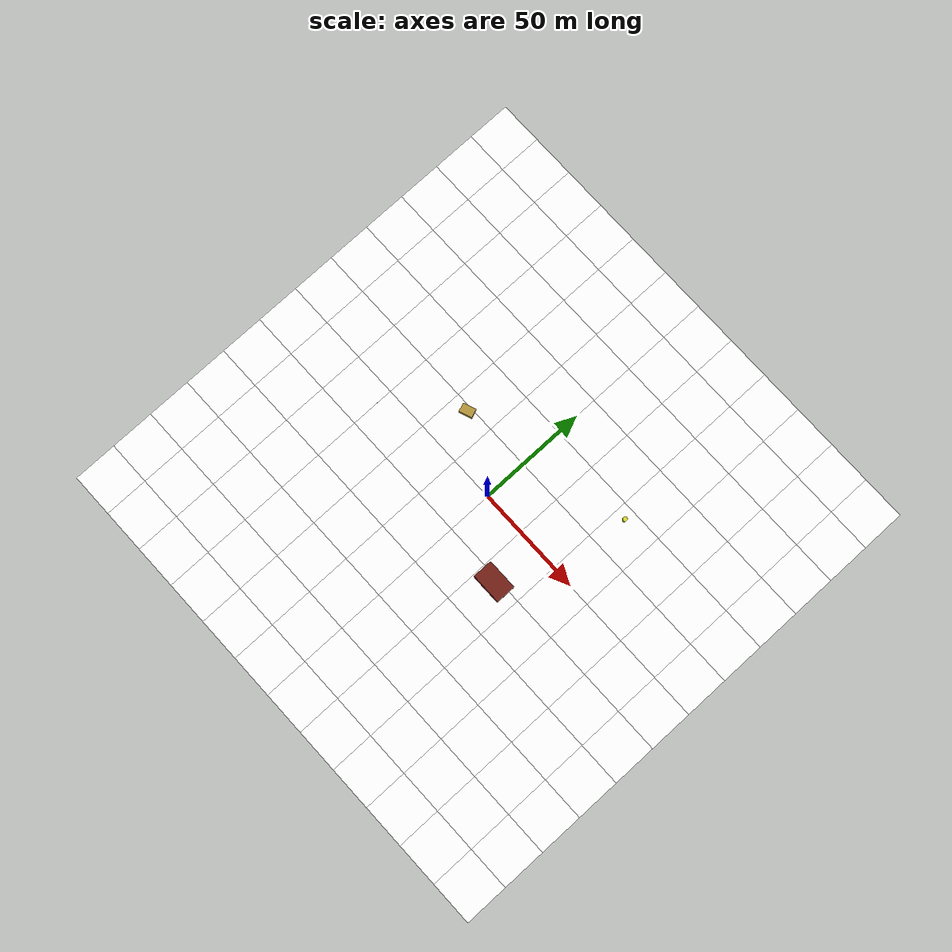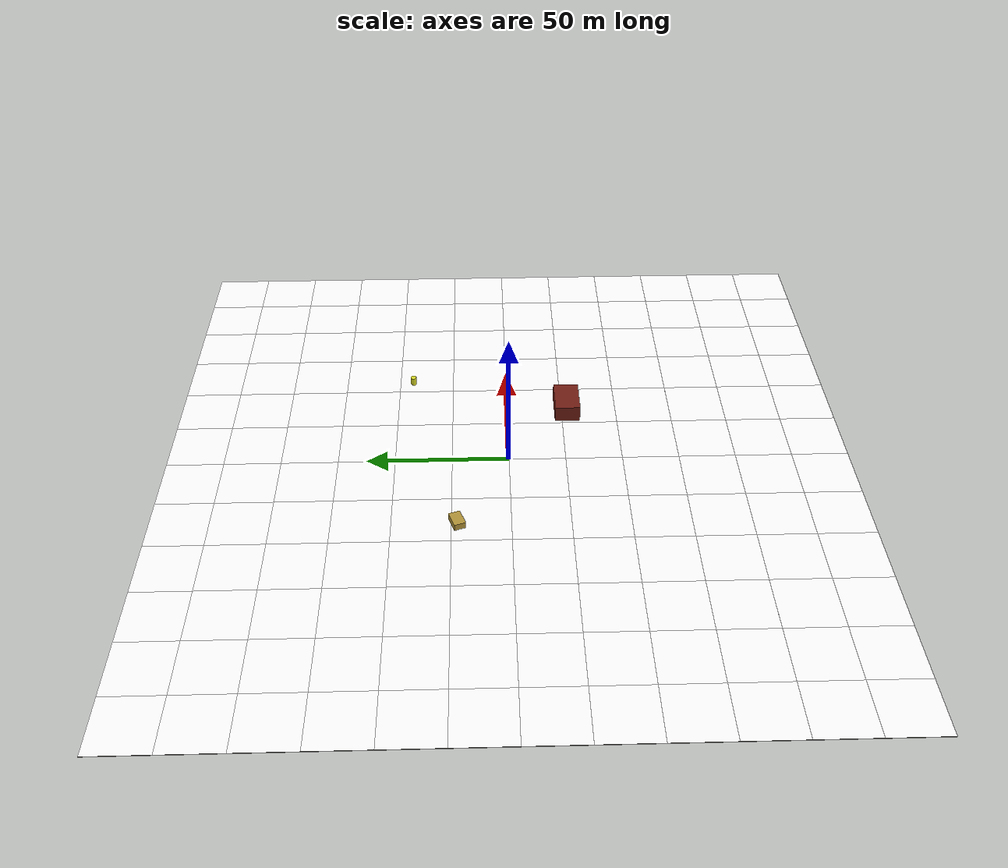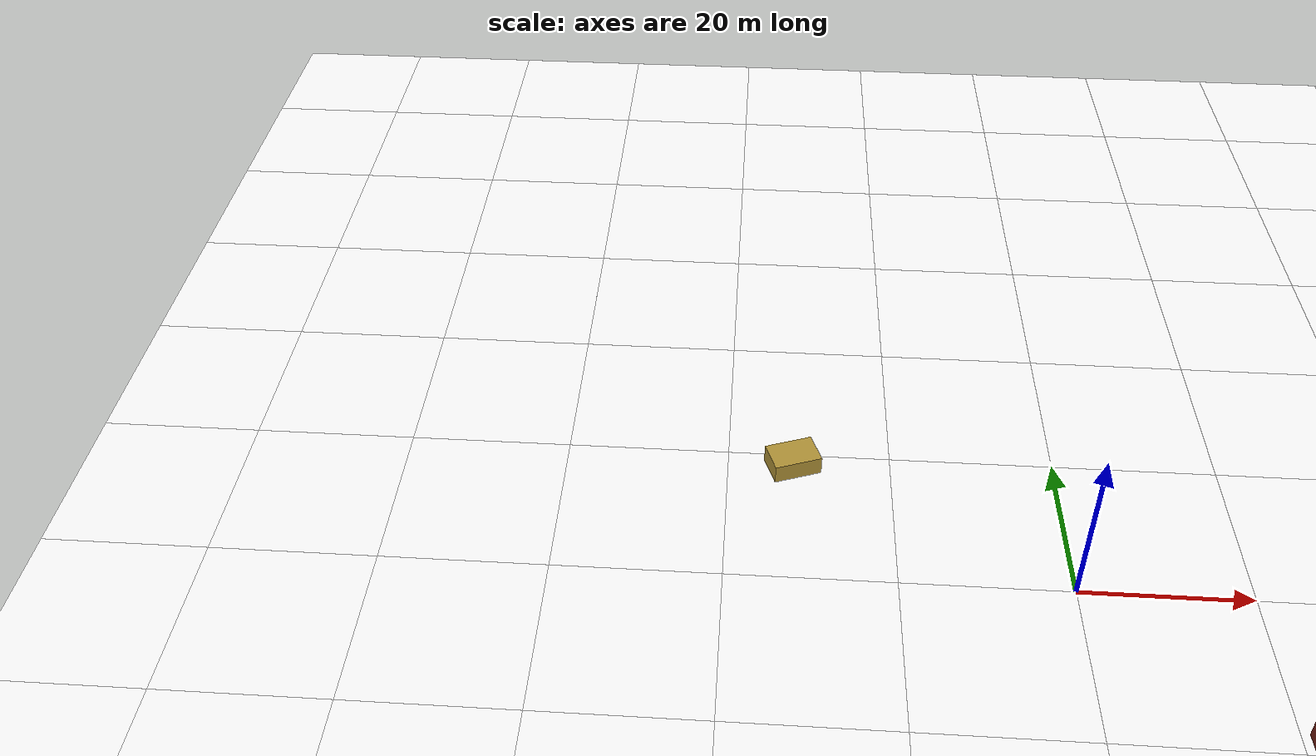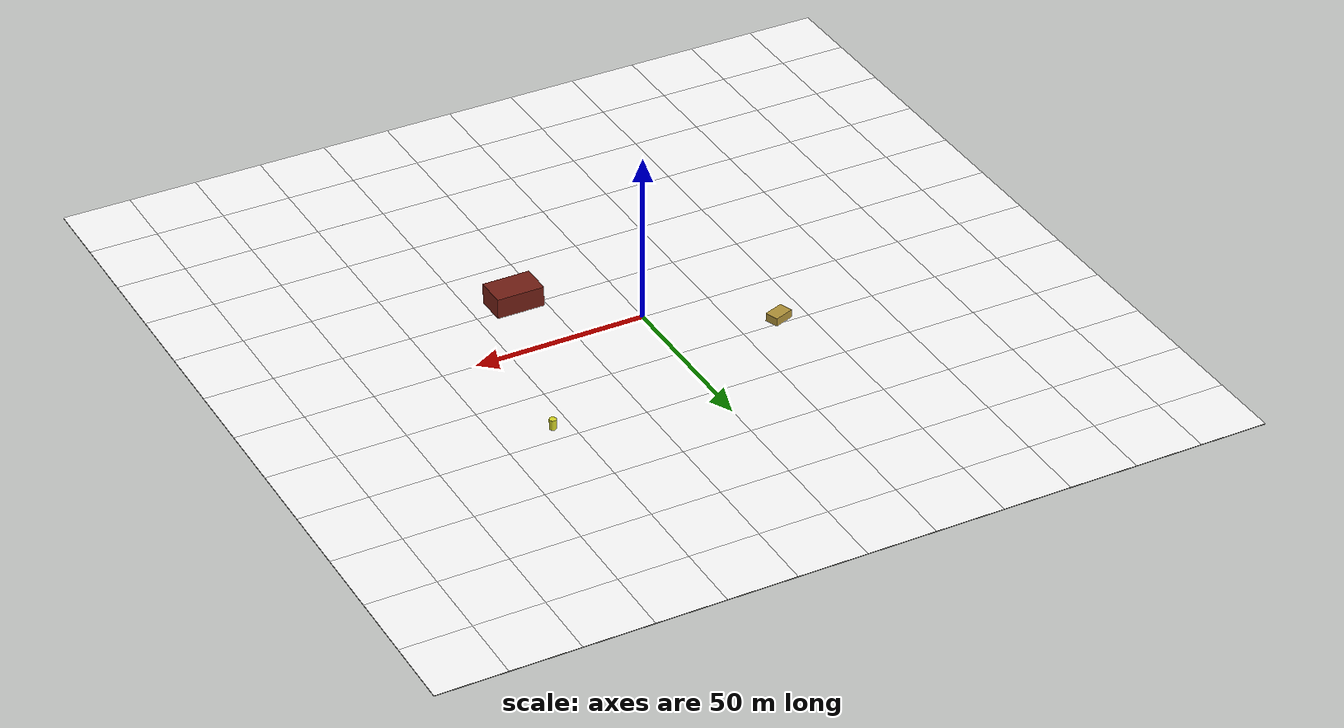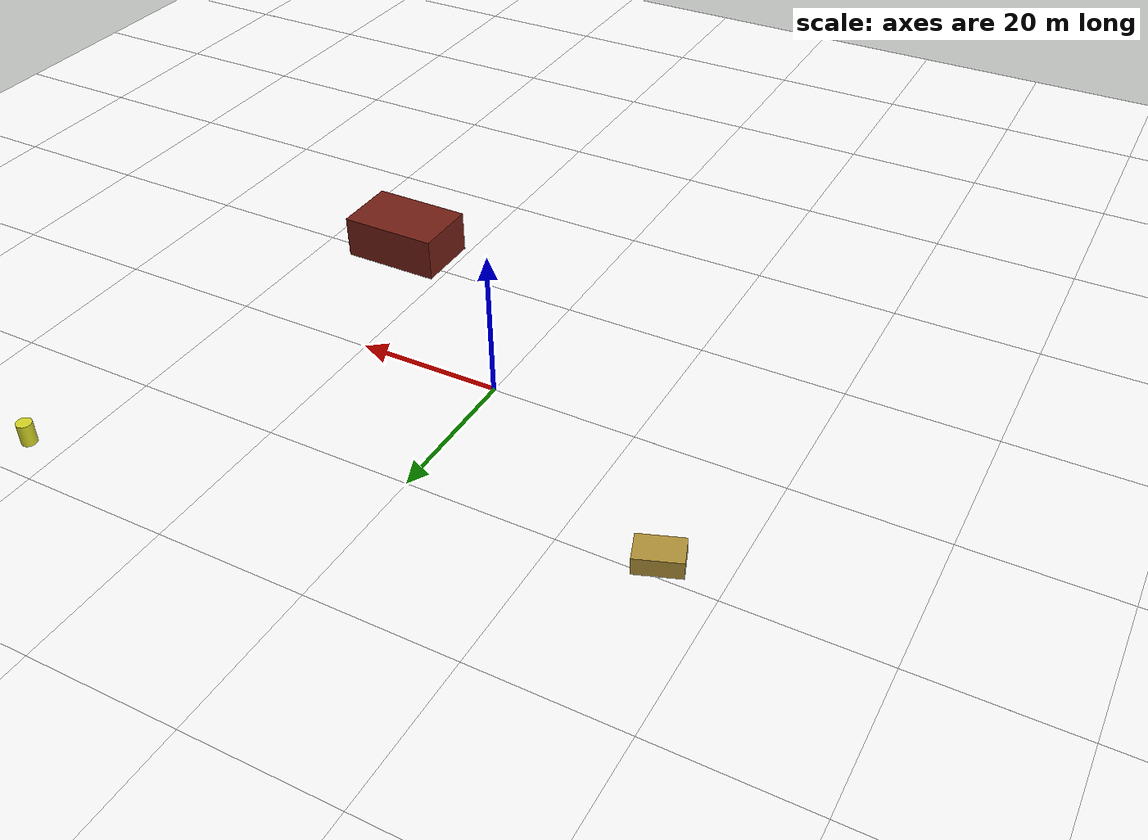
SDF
<?xml version="1.0" ?>
<sdf version="1.9">
  <world name="flat_rural_phototex_noon_wind5ms">

    <scene>
      <ambient>0.550 0.550 0.550 1.000</ambient>
      <background>0.700 0.820 0.950 1.000</background>
      <shadows>false</shadows>
    </scene>

    <light name="sun" type="directional">
      <cast_shadows>false</cast_shadows>
      <pose>0 0 10 0 0 0</pose>
      <diffuse>0.9 0.86 0.76 1</diffuse>
      <specular>0.2 0.2 0.2 1</specular>
      <direction>-0.35 0.15 -0.92</direction>
    </light>

    <wind>
      <linear_velocity>0 5 0</linear_velocity>
    </wind>

    <model name="databoss_ground">
      <static>true</static>
      <link name="ground_link">
        <collision name="ground_collision">
          <pose>0 0 -0.005 0 0 0</pose>
          <geometry>
            <box><size>240 240 0.01</size></box>
          </geometry>
        </collision>

        <collision name="ground_base_collision">
          <pose>0 0 -0.099 0 0 0</pose>
          <geometry>
            <box><size>240 240 0.2</size></box>
          </geometry>
        </collision>
        <visual name="ground_base">
          <pose>0 0 -0.099 0 0 0</pose>
          <geometry>
            <box><size>240 240 0.2</size></box>
          </geometry>
          <material>
            <ambient>0.350 0.350 0.320 1.000</ambient>
            <diffuse>0.350 0.350 0.320 1.000</diffuse>
            <specular>0.02 0.02 0.02 1</specular>
          </material>
        </visual>

        <visual name="tile_0_0">
          <pose>-110 -110 0.002 0 0 0</pose>
          <geometry>
            <box><size>20 20 0.004</size></box>
          </geometry>

          <material>
            <diffuse>1 1 1 1</diffuse>
            <specular>0.05 0.05 0.05 1</specular>
            <pbr>
              <metal>
                <albedo_map>file:///opt/databoss_px4_sim/generated_worlds/textures/ground_speckle_2048.png</albedo_map>
                <roughness>1.0</roughness>
                <metalness>0.0</metalness>
              </metal>
            </pbr>
          </material>
          <!-- material_id: tile_0_0 -->

        </visual>

        <visual name="tile_0_1">
          <pose>-110 -90 0.002 0 0 0</pose>
          <geometry>
            <box><size>20 20 0.004</size></box>
          </geometry>

          <material>
            <diffuse>1 1 1 1</diffuse>
            <specular>0.05 0.05 0.05 1</specular>
            <pbr>
              <metal>
                <albedo_map>file:///opt/databoss_px4_sim/generated_worlds/textures/ground_speckle_2048.png</albedo_map>
                <roughness>1.0</roughness>
                <metalness>0.0</metalness>
              </metal>
            </pbr>
          </material>
          <!-- material_id: tile_0_1 -->

        </visual>

        <visual name="tile_0_2">
          <pose>-110 -70 0.002 0 0 0</pose>
          <geometry>
            <box><size>20 20 0.004</size></box>
          </geometry>

          <material>
            <diffuse>1 1 1 1</diffuse>
            <specular>0.05 0.05 0.05 1</specular>
            <pbr>
              <metal>
                <albedo_map>file:///opt/databoss_px4_sim/generated_worlds/textures/ground_speckle_2048.png</albedo_map>
                <roughness>1.0</roughness>
                <metalness>0.0</metalness>
              </metal>
            </pbr>
          </material>
          <!-- material_id: tile_0_2 -->

        </visual>

        <visual name="tile_0_3">
          <pose>-110 -50 0.002 0 0 0</pose>
          <geometry>
            <box><size>20 20 0.004</size></box>
          </geometry>

          <material>
            <diffuse>1 1 1 1</diffuse>
            <specular>0.05 0.05 0.05 1</specular>
            <pbr>
              <metal>
                <albedo_map>file:///opt/databoss_px4_sim/generated_worlds/textures/ground_speckle_2048.png</albedo_map>
                <roughness>1.0</roughness>
                <metalness>0.0</metalness>
              </metal>
            </pbr>
          </material>
          <!-- material_id: tile_0_3 -->

        </visual>

        <visual name="tile_0_4">
          <pose>-110 -30 0.002 0 0 0</pose>
          <geometry>
            <box><size>20 20 0.004</size></box>
          </geometry>

          <material>
            <diffuse>1 1 1 1</diffuse>
            <specular>0.05 0.05 0.05 1</specular>
            <pbr>
              <metal>
                <albedo_map>file:///opt/databoss_px4_sim/generated_worlds/textures/ground_speckle_2048.png</albedo_map>
                <roughness>1.0</roughness>
                <metalness>0.0</metalness>
              </metal>
            </pbr>
          </material>
          <!-- material_id: tile_0_4 -->

        </visual>

        <visual name="tile_0_5">
          <pose>-110 -10 0.002 0 0 0</pose>
          <geometry>
            <box><size>20 20 0.004</size></box>
          </geometry>

          <material>
            <diffuse>1 1 1 1</diffuse>
            <specular>0.05 0.05 0.05 1</specular>
            <pbr>
              <metal>
                <albedo_map>file:///opt/databoss_px4_sim/generated_worlds/textures/ground_speckle_2048.png</albedo_map>
                <roughness>1.0</roughness>
                <metalness>0.0</metalness>
              </metal>
            </pbr>
          </material>
          <!-- material_id: tile_0_5 -->

        </visual>

        <visual name="tile_0_6">
          <pose>-110 10 0.002 0 0 0</pose>
          <geometry>
            <box><size>20 20 0.004</size></box>
          </geometry>

          <material>
            <diffuse>1 1 1 1</diffuse>
            <specular>0.05 0.05 0.05 1</specular>
            <pbr>
              <metal>
                <albedo_map>file:///opt/databoss_px4_sim/generated_worlds/textures/ground_speckle_2048.png</albedo_map>
                <roughness>1.0</roughness>
                <metalness>0.0</metalness>
              </metal>
            </pbr>
          </material>
          <!-- material_id: tile_0_6 -->

        </visual>

        <visual name="tile_0_7">
          <pose>-110 30 0.002 0 0 0</pose>
          <geometry>
            <box><size>20 20 0.004</size></box>
          </geometry>

          <material>
            <diffuse>1 1 1 1</diffuse>
            <specular>0.05 0.05 0.05 1</specular>
            <pbr>
              <metal>
                <albedo_map>file:///opt/databoss_px4_sim/generated_worlds/textures/ground_speckle_2048.png</albedo_map>
                <roughness>1.0</roughness>
                <metalness>0.0</metalness>
              </metal>
            </pbr>
          </material>
          <!-- material_id: tile_0_7 -->

        </visual>

        <visual name="tile_0_8">
          <pose>-110 50 0.002 0 0 0</pose>
          <geometry>
            <box><size>20 20 0.004</size></box>
          </geometry>

          <material>
            <diffuse>1 1 1 1</diffuse>
            <specular>0.05 0.05 0.05 1</specular>
            <pbr>
              <metal>
                <albedo_map>file:///opt/databoss_px4_sim/generated_worlds/textures/ground_speckle_2048.png</albedo_map>
                <roughness>1.0</roughness>
                <metalness>0.0</metalness>
              </metal>
            </pbr>
          </material>
          <!-- material_id: tile_0_8 -->

        </visual>

        <visual name="tile_0_9">
          <pose>-110 70 0.002 0 0 0</pose>
          <geometry>
            <box><size>20 20 0.004</size></box>
          </geometry>

          <material>
            <diffuse>1 1 1 1</diffuse>
            <specular>0.05 0.05 0.05 1</specular>
            <pbr>
              <metal>
                <albedo_map>file:///opt/databoss_px4_sim/generated_worlds/textures/ground_speckle_2048.png</albedo_map>
                <roughness>1.0</roughness>
                <metalness>0.0</metalness>
              </metal>
            </pbr>
          </material>
          <!-- material_id: tile_0_9 -->

        </visual>

        <visual name="tile_0_10">
          <pose>-110 90 0.002 0 0 0</pose>
          <geometry>
            <box><size>20 20 0.004</size></box>
          </geometry>

          <material>
            <diffuse>1 1 1 1</diffuse>
            <specular>0.05 0.05 0.05 1</specular>
            <pbr>
              <metal>
                <albedo_map>file:///opt/databoss_px4_sim/generated_worlds/textures/ground_speckle_2048.png</albedo_map>
                <roughness>1.0</roughness>
                <metalness>0.0</metalness>
              </metal>
            </pbr>
          </material>
          <!-- material_id: tile_0_10 -->

        </visual>

        <visual name="tile_0_11">
          <pose>-110 110 0.002 0 0 0</pose>
          <geometry>
            <box><size>20 20 0.004</size></box>
          </geometry>

          <material>
            <diffuse>1 1 1 1</diffuse>
            <specular>0.05 0.05 0.05 1</specular>
            <pbr>
              <metal>
                <albedo_map>file:///opt/databoss_px4_sim/generated_worlds/textures/ground_speckle_2048.png</albedo_map>
                <roughness>1.0</roughness>
                <metalness>0.0</metalness>
              </metal>
            </pbr>
          </material>
          <!-- material_id: tile_0_11 -->

        </visual>

        <visual name="tile_1_0">
          <pose>-90 -110 0.002 0 0 0</pose>
          <geometry>
            <box><size>20 20 0.004</size></box>
          </geometry>

          <material>
            <diffuse>1 1 1 1</diffuse>
            <specular>0.05 0.05 0.05 1</specular>
            <pbr>
              <metal>
                <albedo_map>file:///opt/databoss_px4_sim/generated_worlds/textures/ground_speckle_2048.png</albedo_map>
                <roughness>1.0</roughness>
                <metalness>0.0</metalness>
              </metal>
            </pbr>
          </material>
          <!-- material_id: tile_1_0 -->

        </visual>

        <visual name="tile_1_1">
          <pose>-90 -90 0.002 0 0 0</pose>
          <geometry>
            <box><size>20 20 0.004</size></box>
          </geometry>

          <material>
            <diffuse>1 1 1 1</diffuse>
            <specular>0.05 0.05 0.05 1</specular>
            <pbr>
              <metal>
                <albedo_map>file:///opt/databoss_px4_sim/generated_worlds/textures/ground_speckle_2048.png</albedo_map>
                <roughness>1.0</roughness>
                <metalness>0.0</metalness>
              </metal>
            </pbr>
          </material>
          <!-- material_id: tile_1_1 -->

        </visual>

        <visual name="tile_1_2">
          <pose>-90 -70 0.002 0 0 0</pose>
          <geometry>
            <box><size>20 20 0.004</size></box>
          </geometry>

          <material>
            <diffuse>1 1 1 1</diffuse>
            <specular>0.05 0.05 0.05 1</specular>
            <pbr>
              <metal>
                <albedo_map>file:///opt/databoss_px4_sim/generated_worlds/textures/ground_speckle_2048.png</albedo_map>
                <roughness>1.0</roughness>
                <metalness>0.0</metalness>
              </metal>
            </pbr>
          </material>
          <!-- material_id: tile_1_2 -->

        </visual>

        <visual name="tile_1_3">
          <pose>-90 -50 0.002 0 0 0</pose>
          <geometry>
            <box><size>20 20 0.004</size></box>
          </geometry>

          <material>
            <diffuse>1 1 1 1</diffuse>
            <specular>0.05 0.05 0.05 1</specular>
            <pbr>
              <metal>
                <albedo_map>file:///opt/databoss_px4_sim/generated_worlds/textures/ground_speckle_2048.png</albedo_map>
                <roughness>1.0</roughness>
                <metalness>0.0</metalness>
              </metal>
            </pbr>
          </material>
          <!-- material_id: tile_1_3 -->

        </visual>

        <visual name="tile_1_4">
          <pose>-90 -30 0.002 0 0 0</pose>
          <geometry>
            <box><size>20 20 0.004</size></box>
          </geometry>

          <material>
            <diffuse>1 1 1 1</diffuse>
            <specular>0.05 0.05 0.05 1</specular>
            <pbr>
              <metal>
                <albedo_map>file:///opt/databoss_px4_sim/generated_worlds/textures/ground_speckle_2048.png</albedo_map>
                <roughness>1.0</roughness>
                <metalness>0.0</metalness>
              </metal>
            </pbr>
          </material>
          <!-- material_id: tile_1_4 -->

        </visual>

        <visual name="tile_1_5">
          <pose>-90 -10 0.002 0 0 0</pose>
          <geometry>
            <box><size>20 20 0.004</size></box>
          </geometry>

          <material>
            <diffuse>1 1 1 1</diffuse>
            <specular>0.05 0.05 0.05 1</specular>
            <pbr>
              <metal>
                <albedo_map>file:///opt/databoss_px4_sim/generated_worlds/textures/ground_speckle_2048.png</albedo_map>
                <roughness>1.0</roughness>
                <metalness>0.0</metalness>
              </metal>
            </pbr>
          </material>
          <!-- material_id: tile_1_5 -->

        </visual>

        <visual name="tile_1_6">
          <pose>-90 10 0.002 0 0 0</pose>
          <geometry>
            <box><size>20 20 0.004</size></box>
          </geometry>

          <material>
            <diffuse>1 1 1 1</diffuse>
            <specular>0.05 0.05 0.05 1</specular>
            <pbr>
              <metal>
                <albedo_map>file:///opt/databoss_px4_sim/generated_worlds/textures/ground_speckle_2048.png</albedo_map>
                <roughness>1.0</roughness>
                <metalness>0.0</metalness>
              </metal>
            </pbr>
          </material>
          <!-- material_id: tile_1_6 -->

        </visual>

        <visual name="tile_1_7">
          <pose>-90 30 0.002 0 0 0</pose>
          <geometry>
            <box><size>20 20 0.004</size></box>
          </geometry>

          <material>
            <diffuse>1 1 1 1</diffuse>
            <specular>0.05 0.05 0.05 1</specular>
            <pbr>
              <metal>
                <albedo_map>file:///opt/databoss_px4_sim/generated_worlds/textures/ground_speckle_2048.png</albedo_map>
                <roughness>1.0</roughness>
                <metalness>0.0</metalness>
              </metal>
            </pbr>
          </material>
          <!-- material_id: tile_1_7 -->

        </visual>

        <visual name="tile_1_8">
          <pose>-90 50 0.002 0 0 0</pose>
          <geometry>
            <box><size>20 20 0.004</size></box>
          </geometry>

          <material>
            <diffuse>1 1 1 1</diffuse>
            <specular>0.05 0.05 0.05 1</specular>
            <pbr>
              <metal>
                <albedo_map>file:///opt/databoss_px4_sim/generated_worlds/textures/ground_speckle_2048.png</albedo_map>
                <roughness>1.0</roughness>
                <metalness>0.0</metalness>
              </metal>
            </pbr>
          </material>
          <!-- material_id: tile_1_8 -->

        </visual>

        <visual name="tile_1_9">
          <pose>-90 70 0.002 0 0 0</pose>
          <geometry>
            <box><size>20 20 0.004</size></box>
          </geometry>

          <material>
            <diffuse>1 1 1 1</diffuse>
            <specular>0.05 0.05 0.05 1</specular>
            <pbr>
              <metal>
                <albedo_map>file:///opt/databoss_px4_sim/generated_worlds/textures/ground_speckle_2048.png</albedo_map>
                <roughness>1.0</roughness>
                <metalness>0.0</metalness>
              </metal>
            </pbr>
          </material>
          <!-- material_id: tile_1_9 -->

        </visual>

        <visual name="tile_1_10">
          <pose>-90 90 0.002 0 0 0</pose>
          <geometry>
            <box><size>20 20 0.004</size></box>
          </geometry>

          <material>
            <diffuse>1 1 1 1</diffuse>
            <specular>0.05 0.05 0.05 1</specular>
            <pbr>
              <metal>
                <albedo_map>file:///opt/databoss_px4_sim/generated_worlds/textures/ground_speckle_2048.png</albedo_map>
                <roughness>1.0</roughness>
                <metalness>0.0</metalness>
              </metal>
            </pbr>
          </material>
          <!-- material_id: tile_1_10 -->

        </visual>

        <visual name="tile_1_11">
          <pose>-90 110 0.002 0 0 0</pose>
          <geometry>
            <box><size>20 20 0.004</size></box>
          </geometry>

          <material>
            <diffuse>1 1 1 1</diffuse>
            <specular>0.05 0.05 0.05 1</specular>
            <pbr>
              <metal>
                <albedo_map>file:///opt/databoss_px4_sim/generated_worlds/textures/ground_speckle_2048.png</albedo_map>
                <roughness>1.0</roughness>
                <metalness>0.0</metalness>
              </metal>
            </pbr>
          </material>
          <!-- material_id: tile_1_11 -->

        </visual>

        <visual name="tile_2_0">
          <pose>-70 -110 0.002 0 0 0</pose>
          <geometry>
            <box><size>20 20 0.004</size></box>
          </geometry>

          <material>
            <diffuse>1 1 1 1</diffuse>
            <specular>0.05 0.05 0.05 1</specular>
            <pbr>
              <metal>
                <albedo_map>file:///opt/databoss_px4_sim/generated_worlds/textures/ground_speckle_2048.png</albedo_map>
                <roughness>1.0</roughness>
                <metalness>0.0</metalness>
              </metal>
            </pbr>
          </material>
          <!-- material_id: tile_2_0 -->

        </visual>

        <visual name="tile_2_1">
          <pose>-70 -90 0.002 0 0 0</pose>
          <geometry>
            <box><size>20 20 0.004</size></box>
          </geometry>

          <material>
            <diffuse>1 1 1 1</diffuse>
            <specular>0.05 0.05 0.05 1</specular>
            <pbr>
              <metal>
                <albedo_map>file:///opt/databoss_px4_sim/generated_worlds/textures/ground_speckle_2048.png</albedo_map>
                <roughness>1.0</roughness>
                <metalness>0.0</metalness>
              </metal>
            </pbr>
          </material>
          <!-- material_id: tile_2_1 -->

        </visual>

        <visual name="tile_2_2">
          <pose>-70 -70 0.002 0 0 0</pose>
          <geometry>
            <box><size>20 20 0.004</size></box>
          </geometry>

          <material>
            <diffuse>1 1 1 1</diffuse>
            <specular>0.05 0.05 0.05 1</specular>
            <pbr>
              <metal>
                <albedo_map>file:///opt/databoss_px4_sim/generated_worlds/textures/ground_speckle_2048.png</albedo_map>
                <roughness>1.0</roughness>
                <metalness>0.0</metalness>
              </metal>
            </pbr>
          </material>
          <!-- material_id: tile_2_2 -->

        </visual>

        <visual name="tile_2_3">
          <pose>-70 -50 0.002 0 0 0</pose>
          <geometry>
            <box><size>20 20 0.004</size></box>
          </geometry>

          <material>
            <diffuse>1 1 1 1</diffuse>
            <specular>0.05 0.05 0.05 1</specular>
            <pbr>
              <metal>
                <albedo_map>file:///opt/databoss_px4_sim/generated_worlds/textures/ground_speckle_2048.png</albedo_map>
                <roughness>1.0</roughness>
                <metalness>0.0</metalness>
              </metal>
            </pbr>
          </material>
          <!-- material_id: tile_2_3 -->

        </visual>

        <visual name="tile_2_4">
          <pose>-70 -30 0.002 0 0 0</pose>
          <geometry>
            <box><size>20 20 0.004</size></box>
          </geometry>

          <material>
            <diffuse>1 1 1 1</diffuse>
            <specular>0.05 0.05 0.05 1</specular>
            <pbr>
              <metal>
                <albedo_map>file:///opt/databoss_px4_sim/generated_worlds/textures/ground_speckle_2048.png</albedo_map>
                <roughness>1.0</roughness>
                <metalness>0.0</metalness>
              </metal>
            </pbr>
          </material>
          <!-- material_id: tile_2_4 -->

        </visual>

        <visual name="tile_2_5">
          <pose>-70 -10 0.002 0 0 0</pose>
          <geometry>
            <box><size>20 20 0.004</size></box>
          </geometry>

          <material>
            <diffuse>1 1 1 1</diffuse>
            <specular>0.05 0.05 0.05 1</specular>
            <pbr>
              <metal>
                <albedo_map>file:///opt/databoss_px4_sim/generated_worlds/textures/ground_speckle_2048.png</albedo_map>
                <roughness>1.0</roughness>
                <metalness>0.0</metalness>
              </metal>
            </pbr>
          </material>
          <!-- material_id: tile_2_5 -->

        </visual>

        <visual name="tile_2_6">
          <pose>-70 10 0.002 0 0 0</pose>
          <geometry>
            <box><size>20 20 0.004</size></box>
          </geometry>

          <material>
            <diffuse>1 1 1 1</diffuse>
            <specular>0.05 0.05 0.05 1</specular>
            <pbr>
              <metal>
                <albedo_map>file:///opt/databoss_px4_sim/generated_worlds/textures/ground_speckle_2048.png</albedo_map>
                <roughness>1.0</roughness>
                <metalness>0.0</metalness>
              </metal>
            </pbr>
          </material>
          <!-- material_id: tile_2_6 -->

        </visual>

        <visual name="tile_2_7">
          <pose>-70 30 0.002 0 0 0</pose>
          <geometry>
            <box><size>20 20 0.004</size></box>
          </geometry>

          <material>
            <diffuse>1 1 1 1</diffuse>
            <specular>0.05 0.05 0.05 1</specular>
            <pbr>
              <metal>
                <albedo_map>file:///opt/databoss_px4_sim/generated_worlds/textures/ground_speckle_2048.png</albedo_map>
                <roughness>1.0</roughness>
                <metalness>0.0</metalness>
              </metal>
            </pbr>
          </material>
          <!-- material_id: tile_2_7 -->

        </visual>

        <visual name="tile_2_8">
          <pose>-70 50 0.002 0 0 0</pose>
          <geometry>
            <box><size>20 20 0.004</size></box>
          </geometry>

          <material>
            <diffuse>1 1 1 1</diffuse>
            <specular>0.05 0.05 0.05 1</specular>
            <pbr>
              <metal>
                <albedo_map>file:///opt/databoss_px4_sim/generated_worlds/textures/ground_speckle_2048.png</albedo_map>
                <roughness>1.0</roughness>
                <metalness>0.0</metalness>
              </metal>
            </pbr>
          </material>
          <!-- material_id: tile_2_8 -->

        </visual>

        <visual name="tile_2_9">
          <pose>-70 70 0.002 0 0 0</pose>
          <geometry>
            <box><size>20 20 0.004</size></box>
          </geometry>

          <material>
            <diffuse>1 1 1 1</diffuse>
            <specular>0.05 0.05 0.05 1</specular>
            <pbr>
              <metal>
                <albedo_map>file:///opt/databoss_px4_sim/generated_worlds/textures/ground_speckle_2048.png</albedo_map>
                <roughness>1.0</roughness>
                <metalness>0.0</metalness>
              </metal>
            </pbr>
          </material>
          <!-- material_id: tile_2_9 -->

        </visual>

        <visual name="tile_2_10">
          <pose>-70 90 0.002 0 0 0</pose>
          <geometry>
            <box><size>20 20 0.004</size></box>
          </geometry>

          <material>
            <diffuse>1 1 1 1</diffuse>
            <specular>0.05 0.05 0.05 1</specular>
            <pbr>
              <metal>
                <albedo_map>file:///opt/databoss_px4_sim/generated_worlds/textures/ground_speckle_2048.png</albedo_map>
                <roughness>1.0</roughness>
                <metalness>0.0</metalness>
              </metal>
            </pbr>
          </material>
          <!-- material_id: tile_2_10 -->

        </visual>

        <visual name="tile_2_11">
          <pose>-70 110 0.002 0 0 0</pose>
          <geometry>
            <box><size>20 20 0.004</size></box>
          </geometry>

          <material>
            <diffuse>1 1 1 1</diffuse>
            <specular>0.05 0.05 0.05 1</specular>
            <pbr>
              <metal>
                <albedo_map>file:///opt/databoss_px4_sim/generated_worlds/textures/ground_speckle_2048.png</albedo_map>
                <roughness>1.0</roughness>
                <metalness>0.0</metalness>
              </metal>
            </pbr>
          </material>
          <!-- material_id: tile_2_11 -->

        </visual>

        <visual name="tile_3_0">
          <pose>-50 -110 0.002 0 0 0</pose>
          <geometry>
            <box><size>20 20 0.004</size></box>
          </geometry>

          <material>
            <diffuse>1 1 1 1</diffuse>
            <specular>0.05 0.05 0.05 1</specular>
            <pbr>
              <metal>
                <albedo_map>file:///opt/databoss_px4_sim/generated_worlds/textures/ground_speckle_2048.png</albedo_map>
                <roughness>1.0</roughness>
                <metalness>0.0</metalness>
              </metal>
            </pbr>
          </material>
          <!-- material_id: tile_3_0 -->

        </visual>

        <visual name="tile_3_1">
          <pose>-50 -90 0.002 0 0 0</pose>
          <geometry>
            <box><size>20 20 0.004</size></box>
          </geometry>

          <material>
            <diffuse>1 1 1 1</diffuse>
            <specular>0.05 0.05 0.05 1</specular>
            <pbr>
              <metal>
                <albedo_map>file:///opt/databoss_px4_sim/generated_worlds/textures/ground_speckle_2048.png</albedo_map>
                <roughness>1.0</roughness>
                <metalness>0.0</metalness>
              </metal>
            </pbr>
          </material>
          <!-- material_id: tile_3_1 -->

        </visual>

        <visual name="tile_3_2">
          <pose>-50 -70 0.002 0 0 0</pose>
          <geometry>
            <box><size>20 20 0.004</size></box>
          </geometry>

          <material>
            <diffuse>1 1 1 1</diffuse>
            <specular>0.05 0.05 0.05 1</specular>
            <pbr>
              <metal>
                <albedo_map>file:///opt/databoss_px4_sim/generated_worlds/textures/ground_speckle_2048.png</albedo_map>
                <roughness>1.0</roughness>
                <metalness>0.0</metalness>
              </metal>
            </pbr>
          </material>
          <!-- material_id: tile_3_2 -->

        </visual>

        <visual name="tile_3_3">
          <pose>-50 -50 0.002 0 0 0</pose>
          <geometry>
            <box><size>20 20 0.004</size></box>
          </geometry>

          <material>
            <diffuse>1 1 1 1</diffuse>
            <specular>0.05 0.05 0.05 1</specular>
            <pbr>
              <metal>
                <albedo_map>file:///opt/databoss_px4_sim/generated_worlds/textures/ground_speckle_2048.png</albedo_map>
                <roughness>1.0</roughness>
                <metalness>0.0</metalness>
              </metal>
            </pbr>
          </material>
          <!-- material_id: tile_3_3 -->

        </visual>

        <visual name="tile_3_4">
          <pose>-50 -30 0.002 0 0 0</pose>
          <geometry>
            <box><size>20 20 0.004</size></box>
          </geometry>

          <material>
            <diffuse>1 1 1 1</diffuse>
            <specular>0.05 0.05 0.05 1</specular>
            <pbr>
              <metal>
                <albedo_map>file:///opt/databoss_px4_sim/generated_worlds/textures/ground_speckle_2048.png</albedo_map>
                <roughness>1.0</roughness>
                <metalness>0.0</metalness>
              </metal>
            </pbr>
          </material>
          <!-- material_id: tile_3_4 -->

        </visual>

        <visual name="tile_3_5">
          <pose>-50 -10 0.002 0 0 0</pose>
          <geometry>
            <box><size>20 20 0.004</size></box>
          </geometry>

          <material>
            <diffuse>1 1 1 1</diffuse>
            <specular>0.05 0.05 0.05 1</specular>
            <pbr>
              <metal>
                <albedo_map>file:///opt/databoss_px4_sim/generated_worlds/textures/ground_speckle_2048.png</albedo_map>
                <roughness>1.0</roughness>
                <metalness>0.0</metalness>
              </metal>
            </pbr>
          </material>
          <!-- material_id: tile_3_5 -->

        </visual>

        <visual name="tile_3_6">
          <pose>-50 10 0.002 0 0 0</pose>
          <geometry>
            <box><size>20 20 0.004</size></box>
          </geometry>

          <material>
            <diffuse>1 1 1 1</diffuse>
            <specular>0.05 0.05 0.05 1</specular>
            <pbr>
              <metal>
                <albedo_map>file:///opt/databoss_px4_sim/generated_worlds/textures/ground_speckle_2048.png</albedo_map>
                <roughness>1.0</roughness>
                <metalness>0.0</metalness>
              </metal>
            </pbr>
          </material>
          <!-- material_id: tile_3_6 -->

        </visual>

        <visual name="tile_3_7">
          <pose>-50 30 0.002 0 0 0</pose>
          <geometry>
            <box><size>20 20 0.004</size></box>
          </geometry>

          <material>
            <diffuse>1 1 1 1</diffuse>
            <specular>0.05 0.05 0.05 1</specular>
            <pbr>
              <metal>
                <albedo_map>file:///opt/databoss_px4_sim/generated_worlds/textures/ground_speckle_2048.png</albedo_map>
                <roughness>1.0</roughness>
                <metalness>0.0</metalness>
              </metal>
            </pbr>
          </material>
          <!-- material_id: tile_3_7 -->

        </visual>

        <visual name="tile_3_8">
          <pose>-50 50 0.002 0 0 0</pose>
          <geometry>
            <box><size>20 20 0.004</size></box>
          </geometry>

          <material>
            <diffuse>1 1 1 1</diffuse>
            <specular>0.05 0.05 0.05 1</specular>
            <pbr>
              <metal>
                <albedo_map>file:///opt/databoss_px4_sim/generated_worlds/textures/ground_speckle_2048.png</albedo_map>
                <roughness>1.0</roughness>
                <metalness>0.0</metalness>
              </metal>
            </pbr>
          </material>
          <!-- material_id: tile_3_8 -->

        </visual>

        <visual name="tile_3_9">
          <pose>-50 70 0.002 0 0 0</pose>
          <geometry>
            <box><size>20 20 0.004</size></box>
          </geometry>

          <material>
            <diffuse>1 1 1 1</diffuse>
            <specular>0.05 0.05 0.05 1</specular>
            <pbr>
              <metal>
                <albedo_map>file:///opt/databoss_px4_sim/generated_worlds/textures/ground_speckle_2048.png</albedo_map>
                <roughness>1.0</roughness>
                <metalness>0.0</metalness>
              </metal>
            </pbr>
          </material>
          <!-- material_id: tile_3_9 -->

        </visual>

        <visual name="tile_3_10">
          <pose>-50 90 0.002 0 0 0</pose>
          <geometry>
            <box><size>20 20 0.004</size></box>
          </geometry>

          <material>
            <diffuse>1 1 1 1</diffuse>
            <specular>0.05 0.05 0.05 1</specular>
            <pbr>
              <metal>
                <albedo_map>file:///opt/databoss_px4_sim/generated_worlds/textures/ground_speckle_2048.png</albedo_map>
                <roughness>1.0</roughness>
                <metalness>0.0</metalness>
              </metal>
            </pbr>
          </material>
          <!-- material_id: tile_3_10 -->

        </visual>

        <visual name="tile_3_11">
          <pose>-50 110 0.002 0 0 0</pose>
          <geometry>
            <box><size>20 20 0.004</size></box>
          </geometry>

          <material>
            <diffuse>1 1 1 1</diffuse>
            <specular>0.05 0.05 0.05 1</specular>
            <pbr>
              <metal>
                <albedo_map>file:///opt/databoss_px4_sim/generated_worlds/textures/ground_speckle_2048.png</albedo_map>
                <roughness>1.0</roughness>
                <metalness>0.0</metalness>
              </metal>
            </pbr>
          </material>
          <!-- material_id: tile_3_11 -->

        </visual>

        <visual name="tile_4_0">
          <pose>-30 -110 0.002 0 0 0</pose>
          <geometry>
            <box><size>20 20 0.004</size></box>
          </geometry>

          <material>
            <diffuse>1 1 1 1</diffuse>
            <specular>0.05 0.05 0.05 1</specular>
            <pbr>
              <metal>
                <albedo_map>file:///opt/databoss_px4_sim/generated_worlds/textures/ground_speckle_2048.png</albedo_map>
                <roughness>1.0</roughness>
                <metalness>0.0</metalness>
              </metal>
            </pbr>
          </material>
          <!-- material_id: tile_4_0 -->

        </visual>

        <visual name="tile_4_1">
          <pose>-30 -90 0.002 0 0 0</pose>
          <geometry>
            <box><size>20 20 0.004</size></box>
          </geometry>

          <material>
            <diffuse>1 1 1 1</diffuse>
            <specular>0.05 0.05 0.05 1</specular>
            <pbr>
              <metal>
                <albedo_map>file:///opt/databoss_px4_sim/generated_worlds/textures/ground_speckle_2048.png</albedo_map>
                <roughness>1.0</roughness>
                <metalness>0.0</metalness>
              </metal>
            </pbr>
          </material>
          <!-- material_id: tile_4_1 -->

        </visual>

        <visual name="tile_4_2">
          <pose>-30 -70 0.002 0 0 0</pose>
          <geometry>
            <box><size>20 20 0.004</size></box>
          </geometry>

          <material>
            <diffuse>1 1 1 1</diffuse>
            <specular>0.05 0.05 0.05 1</specular>
            <pbr>
              <metal>
                <albedo_map>file:///opt/databoss_px4_sim/generated_worlds/textures/ground_speckle_2048.png</albedo_map>
                <roughness>1.0</roughness>
                <metalness>0.0</metalness>
              </metal>
            </pbr>
          </material>
          <!-- material_id: tile_4_2 -->

        </visual>

        <visual name="tile_4_3">
          <pose>-30 -50 0.002 0 0 0</pose>
          <geometry>
            <box><size>20 20 0.004</size></box>
          </geometry>

          <material>
            <diffuse>1 1 1 1</diffuse>
            <specular>0.05 0.05 0.05 1</specular>
            <pbr>
              <metal>
                <albedo_map>file:///opt/databoss_px4_sim/generated_worlds/textures/ground_speckle_2048.png</albedo_map>
                <roughness>1.0</roughness>
                <metalness>0.0</metalness>
              </metal>
            </pbr>
          </material>
          <!-- material_id: tile_4_3 -->

        </visual>

        <visual name="tile_4_4">
          <pose>-30 -30 0.002 0 0 0</pose>
          <geometry>
            <box><size>20 20 0.004</size></box>
          </geometry>

          <material>
            <diffuse>1 1 1 1</diffuse>
            <specular>0.05 0.05 0.05 1</specular>
            <pbr>
              <metal>
                <albedo_map>file:///opt/databoss_px4_sim/generated_worlds/textures/ground_speckle_2048.png</albedo_map>
                <roughness>1.0</roughness>
                <metalness>0.0</metalness>
              </metal>
            </pbr>
          </material>
          <!-- material_id: tile_4_4 -->

        </visual>

        <visual name="tile_4_5">
          <pose>-30 -10 0.002 0 0 0</pose>
          <geometry>
            <box><size>20 20 0.004</size></box>
          </geometry>

          <material>
            <diffuse>1 1 1 1</diffuse>
            <specular>0.05 0.05 0.05 1</specular>
            <pbr>
              <metal>
                <albedo_map>file:///opt/databoss_px4_sim/generated_worlds/textures/ground_speckle_2048.png</albedo_map>
                <roughness>1.0</roughness>
                <metalness>0.0</metalness>
              </metal>
            </pbr>
          </material>
          <!-- material_id: tile_4_5 -->

        </visual>

        <visual name="tile_4_6">
          <pose>-30 10 0.002 0 0 0</pose>
          <geometry>
            <box><size>20 20 0.004</size></box>
          </geometry>

          <material>
            <diffuse>1 1 1 1</diffuse>
            <specular>0.05 0.05 0.05 1</specular>
            <pbr>
              <metal>
                <albedo_map>file:///opt/databoss_px4_sim/generated_worlds/textures/ground_speckle_2048.png</albedo_map>
                <roughness>1.0</roughness>
                <metalness>0.0</metalness>
              </metal>
            </pbr>
          </material>
          <!-- material_id: tile_4_6 -->

        </visual>

        <visual name="tile_4_7">
          <pose>-30 30 0.002 0 0 0</pose>
          <geometry>
            <box><size>20 20 0.004</size></box>
          </geometry>

          <material>
            <diffuse>1 1 1 1</diffuse>
            <specular>0.05 0.05 0.05 1</specular>
            <pbr>
              <metal>
                <albedo_map>file:///opt/databoss_px4_sim/generated_worlds/textures/ground_speckle_2048.png</albedo_map>
                <roughness>1.0</roughness>
                <metalness>0.0</metalness>
              </metal>
            </pbr>
          </material>
          <!-- material_id: tile_4_7 -->

        </visual>

        <visual name="tile_4_8">
          <pose>-30 50 0.002 0 0 0</pose>
          <geometry>
            <box><size>20 20 0.004</size></box>
          </geometry>

          <material>
            <diffuse>1 1 1 1</diffuse>
            <specular>0.05 0.05 0.05 1</specular>
            <pbr>
              <metal>
                <albedo_map>file:///opt/databoss_px4_sim/generated_worlds/textures/ground_speckle_2048.png</albedo_map>
                <roughness>1.0</roughness>
                <metalness>0.0</metalness>
              </metal>
            </pbr>
          </material>
          <!-- material_id: tile_4_8 -->

        </visual>

        <visual name="tile_4_9">
          <pose>-30 70 0.002 0 0 0</pose>
          <geometry>
            <box><size>20 20 0.004</size></box>
          </geometry>

          <material>
            <diffuse>1 1 1 1</diffuse>
            <specular>0.05 0.05 0.05 1</specular>
            <pbr>
              <metal>
                <albedo_map>file:///opt/databoss_px4_sim/generated_worlds/textures/ground_speckle_2048.png</albedo_map>
                <roughness>1.0</roughness>
                <metalness>0.0</metalness>
              </metal>
            </pbr>
          </material>
          <!-- material_id: tile_4_9 -->

        </visual>

        <visual name="tile_4_10">
          <pose>-30 90 0.002 0 0 0</pose>
          <geometry>
            <box><size>20 20 0.004</size></box>
          </geometry>

          <material>
            <diffuse>1 1 1 1</diffuse>
            <specular>0.05 0.05 0.05 1</specular>
            <pbr>
              <metal>
                <albedo_map>file:///opt/databoss_px4_sim/generated_worlds/textures/ground_speckle_2048.png</albedo_map>
                <roughness>1.0</roughness>
                <metalness>0.0</metalness>
              </metal>
            </pbr>
          </material>
          <!-- material_id: tile_4_10 -->

        </visual>

        <visual name="tile_4_11">
          <pose>-30 110 0.002 0 0 0</pose>
          <geometry>
            <box><size>20 20 0.004</size></box>
          </geometry>

          <material>
            <diffuse>1 1 1 1</diffuse>
            <specular>0.05 0.05 0.05 1</specular>
            <pbr>
              <metal>
                <albedo_map>file:///opt/databoss_px4_sim/generated_worlds/textures/ground_speckle_2048.png</albedo_map>
                <roughness>1.0</roughness>
                <metalness>0.0</metalness>
              </metal>
            </pbr>
          </material>
          <!-- material_id: tile_4_11 -->

        </visual>

        <visual name="tile_5_0">
          <pose>-10 -110 0.002 0 0 0</pose>
          <geometry>
            <box><size>20 20 0.004</size></box>
          </geometry>

          <material>
            <diffuse>1 1 1 1</diffuse>
            <specular>0.05 0.05 0.05 1</specular>
            <pbr>
              <metal>
                <albedo_map>file:///opt/databoss_px4_sim/generated_worlds/textures/ground_speckle_2048.png</albedo_map>
                <roughness>1.0</roughness>
                <metalness>0.0</metalness>
              </metal>
            </pbr>
          </material>
          <!-- material_id: tile_5_0 -->

        </visual>

        <visual name="tile_5_1">
          <pose>-10 -90 0.002 0 0 0</pose>
          <geometry>
            <box><size>20 20 0.004</size></box>
          </geometry>

          <material>
            <diffuse>1 1 1 1</diffuse>
            <specular>0.05 0.05 0.05 1</specular>
            <pbr>
              <metal>
                <albedo_map>file:///opt/databoss_px4_sim/generated_worlds/textures/ground_speckle_2048.png</albedo_map>
                <roughness>1.0</roughness>
                <metalness>0.0</metalness>
              </metal>
            </pbr>
          </material>
          <!-- material_id: tile_5_1 -->

        </visual>

        <visual name="tile_5_2">
          <pose>-10 -70 0.002 0 0 0</pose>
          <geometry>
            <box><size>20 20 0.004</size></box>
          </geometry>

          <material>
            <diffuse>1 1 1 1</diffuse>
            <specular>0.05 0.05 0.05 1</specular>
            <pbr>
              <metal>
                <albedo_map>file:///opt/databoss_px4_sim/generated_worlds/textures/ground_speckle_2048.png</albedo_map>
                <roughness>1.0</roughness>
                <metalness>0.0</metalness>
              </metal>
            </pbr>
          </material>
          <!-- material_id: tile_5_2 -->

        </visual>

        <visual name="tile_5_3">
          <pose>-10 -50 0.002 0 0 0</pose>
          <geometry>
            <box><size>20 20 0.004</size></box>
          </geometry>

          <material>
            <diffuse>1 1 1 1</diffuse>
            <specular>0.05 0.05 0.05 1</specular>
            <pbr>
              <metal>
                <albedo_map>file:///opt/databoss_px4_sim/generated_worlds/textures/ground_speckle_2048.png</albedo_map>
                <roughness>1.0</roughness>
                <metalness>0.0</metalness>
              </metal>
            </pbr>
          </material>
          <!-- material_id: tile_5_3 -->

        </visual>

        <visual name="tile_5_4">
          <pose>-10 -30 0.002 0 0 0</pose>
          <geometry>
            <box><size>20 20 0.004</size></box>
          </geometry>

          <material>
            <diffuse>1 1 1 1</diffuse>
            <specular>0.05 0.05 0.05 1</specular>
            <pbr>
              <metal>
                <albedo_map>file:///opt/databoss_px4_sim/generated_worlds/textures/ground_speckle_2048.png</albedo_map>
                <roughness>1.0</roughness>
                <metalness>0.0</metalness>
              </metal>
            </pbr>
          </material>
          <!-- material_id: tile_5_4 -->

        </visual>

        <visual name="tile_5_5">
          <pose>-10 -10 0.002 0 0 0</pose>
          <geometry>
            <box><size>20 20 0.004</size></box>
          </geometry>

          <material>
            <diffuse>1 1 1 1</diffuse>
            <specular>0.05 0.05 0.05 1</specular>
            <pbr>
              <metal>
                <albedo_map>file:///opt/databoss_px4_sim/generated_worlds/textures/ground_speckle_2048.png</albedo_map>
                <roughness>1.0</roughness>
                <metalness>0.0</metalness>
              </metal>
            </pbr>
          </material>
          <!-- material_id: tile_5_5 -->

        </visual>

        <visual name="tile_5_6">
          <pose>-10 10 0.002 0 0 0</pose>
          <geometry>
            <box><size>20 20 0.004</size></box>
          </geometry>

          <material>
            <diffuse>1 1 1 1</diffuse>
            <specular>0.05 0.05 0.05 1</specular>
            <pbr>
              <metal>
                <albedo_map>file:///opt/databoss_px4_sim/generated_worlds/textures/ground_speckle_2048.png</albedo_map>
                <roughness>1.0</roughness>
                <metalness>0.0</metalness>
              </metal>
            </pbr>
          </material>
          <!-- material_id: tile_5_6 -->

        </visual>

        <visual name="tile_5_7">
          <pose>-10 30 0.002 0 0 0</pose>
          <geometry>
            <box><size>20 20 0.004</size></box>
          </geometry>

          <material>
            <diffuse>1 1 1 1</diffuse>
            <specular>0.05 0.05 0.05 1</specular>
            <pbr>
              <metal>
                <albedo_map>file:///opt/databoss_px4_sim/generated_worlds/textures/ground_speckle_2048.png</albedo_map>
                <roughness>1.0</roughness>
                <metalness>0.0</metalness>
              </metal>
            </pbr>
          </material>
          <!-- material_id: tile_5_7 -->

        </visual>

        <visual name="tile_5_8">
          <pose>-10 50 0.002 0 0 0</pose>
          <geometry>
            <box><size>20 20 0.004</size></box>
          </geometry>

          <material>
            <diffuse>1 1 1 1</diffuse>
            <specular>0.05 0.05 0.05 1</specular>
            <pbr>
              <metal>
                <albedo_map>file:///opt/databoss_px4_sim/generated_worlds/textures/ground_speckle_2048.png</albedo_map>
                <roughness>1.0</roughness>
                <metalness>0.0</metalness>
              </metal>
            </pbr>
          </material>
          <!-- material_id: tile_5_8 -->

        </visual>

        <visual name="tile_5_9">
          <pose>-10 70 0.002 0 0 0</pose>
          <geometry>
            <box><size>20 20 0.004</size></box>
          </geometry>

          <material>
            <diffuse>1 1 1 1</diffuse>
            <specular>0.05 0.05 0.05 1</specular>
            <pbr>
              <metal>
                <albedo_map>file:///opt/databoss_px4_sim/generated_worlds/textures/ground_speckle_2048.png</albedo_map>
                <roughness>1.0</roughness>
                <metalness>0.0</metalness>
              </metal>
            </pbr>
          </material>
          <!-- material_id: tile_5_9 -->

        </visual>

        <visual name="tile_5_10">
          <pose>-10 90 0.002 0 0 0</pose>
          <geometry>
            <box><size>20 20 0.004</size></box>
          </geometry>

          <material>
            <diffuse>1 1 1 1</diffuse>
            <specular>0.05 0.05 0.05 1</specular>
            <pbr>
              <metal>
                <albedo_map>file:///opt/databoss_px4_sim/generated_worlds/textures/ground_speckle_2048.png</albedo_map>
                <roughness>1.0</roughness>
                <metalness>0.0</metalness>
              </metal>
            </pbr>
          </material>
          <!-- material_id: tile_5_10 -->

        </visual>

        <visual name="tile_5_11">
          <pose>-10 110 0.002 0 0 0</pose>
          <geometry>
            <box><size>20 20 0.004</size></box>
          </geometry>

          <material>
            <diffuse>1 1 1 1</diffuse>
            <specular>0.05 0.05 0.05 1</specular>
            <pbr>
              <metal>
                <albedo_map>file:///opt/databoss_px4_sim/generated_worlds/textures/ground_speckle_2048.png</albedo_map>
                <roughness>1.0</roughness>
                <metalness>0.0</metalness>
              </metal>
            </pbr>
          </material>
          <!-- material_id: tile_5_11 -->

        </visual>

        <visual name="tile_6_0">
          <pose>10 -110 0.002 0 0 0</pose>
          <geometry>
            <box><size>20 20 0.004</size></box>
          </geometry>

          <material>
            <diffuse>1 1 1 1</diffuse>
            <specular>0.05 0.05 0.05 1</specular>
            <pbr>
              <metal>
                <albedo_map>file:///opt/databoss_px4_sim/generated_worlds/textures/ground_speckle_2048.png</albedo_map>
                <roughness>1.0</roughness>
                <metalness>0.0</metalness>
              </metal>
            </pbr>
          </material>
          <!-- material_id: tile_6_0 -->

        </visual>

        <visual name="tile_6_1">
          <pose>10 -90 0.002 0 0 0</pose>
          <geometry>
            <box><size>20 20 0.004</size></box>
          </geometry>

          <material>
            <diffuse>1 1 1 1</diffuse>
            <specular>0.05 0.05 0.05 1</specular>
            <pbr>
              <metal>
                <albedo_map>file:///opt/databoss_px4_sim/generated_worlds/textures/ground_speckle_2048.png</albedo_map>
                <roughness>1.0</roughness>
                <metalness>0.0</metalness>
              </metal>
            </pbr>
          </material>
          <!-- material_id: tile_6_1 -->

        </visual>

        <visual name="tile_6_2">
          <pose>10 -70 0.002 0 0 0</pose>
          <geometry>
            <box><size>20 20 0.004</size></box>
          </geometry>

          <material>
            <diffuse>1 1 1 1</diffuse>
            <specular>0.05 0.05 0.05 1</specular>
            <pbr>
              <metal>
                <albedo_map>file:///opt/databoss_px4_sim/generated_worlds/textures/ground_speckle_2048.png</albedo_map>
                <roughness>1.0</roughness>
                <metalness>0.0</metalness>
              </metal>
            </pbr>
          </material>
          <!-- material_id: tile_6_2 -->

        </visual>

        <visual name="tile_6_3">
          <pose>10 -50 0.002 0 0 0</pose>
          <geometry>
            <box><size>20 20 0.004</size></box>
          </geometry>

          <material>
            <diffuse>1 1 1 1</diffuse>
            <specular>0.05 0.05 0.05 1</specular>
            <pbr>
              <metal>
                <albedo_map>file:///opt/databoss_px4_sim/generated_worlds/textures/ground_speckle_2048.png</albedo_map>
                <roughness>1.0</roughness>
                <metalness>0.0</metalness>
              </metal>
            </pbr>
          </material>
          <!-- material_id: tile_6_3 -->

        </visual>

        <visual name="tile_6_4">
          <pose>10 -30 0.002 0 0 0</pose>
          <geometry>
            <box><size>20 20 0.004</size></box>
          </geometry>

          <material>
            <diffuse>1 1 1 1</diffuse>
            <specular>0.05 0.05 0.05 1</specular>
            <pbr>
              <metal>
                <albedo_map>file:///opt/databoss_px4_sim/generated_worlds/textures/ground_speckle_2048.png</albedo_map>
                <roughness>1.0</roughness>
                <metalness>0.0</metalness>
              </metal>
            </pbr>
          </material>
          <!-- material_id: tile_6_4 -->

        </visual>

        <visual name="tile_6_5">
          <pose>10 -10 0.002 0 0 0</pose>
          <geometry>
            <box><size>20 20 0.004</size></box>
          </geometry>

          <material>
            <diffuse>1 1 1 1</diffuse>
            <specular>0.05 0.05 0.05 1</specular>
            <pbr>
              <metal>
                <albedo_map>file:///opt/databoss_px4_sim/generated_worlds/textures/ground_speckle_2048.png</albedo_map>
                <roughness>1.0</roughness>
                <metalness>0.0</metalness>
              </metal>
            </pbr>
          </material>
          <!-- material_id: tile_6_5 -->

        </visual>

        <visual name="tile_6_6">
          <pose>10 10 0.002 0 0 0</pose>
          <geometry>
            <box><size>20 20 0.004</size></box>
          </geometry>

          <material>
            <diffuse>1 1 1 1</diffuse>
            <specular>0.05 0.05 0.05 1</specular>
            <pbr>
              <metal>
                <albedo_map>file:///opt/databoss_px4_sim/generated_worlds/textures/ground_speckle_2048.png</albedo_map>
                <roughness>1.0</roughness>
                <metalness>0.0</metalness>
              </metal>
            </pbr>
          </material>
          <!-- material_id: tile_6_6 -->

        </visual>

        <visual name="tile_6_7">
          <pose>10 30 0.002 0 0 0</pose>
          <geometry>
            <box><size>20 20 0.004</size></box>
          </geometry>

          <material>
            <diffuse>1 1 1 1</diffuse>
            <specular>0.05 0.05 0.05 1</specular>
            <pbr>
              <metal>
                <albedo_map>file:///opt/databoss_px4_sim/generated_worlds/textures/ground_speckle_2048.png</albedo_map>
                <roughness>1.0</roughness>
                <metalness>0.0</metalness>
              </metal>
            </pbr>
          </material>
          <!-- material_id: tile_6_7 -->

        </visual>

        <visual name="tile_6_8">
          <pose>10 50 0.002 0 0 0</pose>
          <geometry>
            <box><size>20 20 0.004</size></box>
          </geometry>

          <material>
            <diffuse>1 1 1 1</diffuse>
            <specular>0.05 0.05 0.05 1</specular>
            <pbr>
              <metal>
                <albedo_map>file:///opt/databoss_px4_sim/generated_worlds/textures/ground_speckle_2048.png</albedo_map>
                <roughness>1.0</roughness>
                <metalness>0.0</metalness>
              </metal>
            </pbr>
          </material>
          <!-- material_id: tile_6_8 -->

        </visual>

        <visual name="tile_6_9">
          <pose>10 70 0.002 0 0 0</pose>
          <geometry>
            <box><size>20 20 0.004</size></box>
          </geometry>

          <material>
            <diffuse>1 1 1 1</diffuse>
            <specular>0.05 0.05 0.05 1</specular>
            <pbr>
              <metal>
                <albedo_map>file:///opt/databoss_px4_sim/generated_worlds/textures/ground_speckle_2048.png</albedo_map>
                <roughness>1.0</roughness>
                <metalness>0.0</metalness>
              </metal>
            </pbr>
          </material>
          <!-- material_id: tile_6_9 -->

        </visual>

        <visual name="tile_6_10">
          <pose>10 90 0.002 0 0 0</pose>
          <geometry>
            <box><size>20 20 0.004</size></box>
          </geometry>

          <material>
            <diffuse>1 1 1 1</diffuse>
            <specular>0.05 0.05 0.05 1</specular>
            <pbr>
              <metal>
                <albedo_map>file:///opt/databoss_px4_sim/generated_worlds/textures/ground_speckle_2048.png</albedo_map>
                <roughness>1.0</roughness>
                <metalness>0.0</metalness>
              </metal>
            </pbr>
          </material>
          <!-- material_id: tile_6_10 -->

        </visual>

        <visual name="tile_6_11">
          <pose>10 110 0.002 0 0 0</pose>
          <geometry>
            <box><size>20 20 0.004</size></box>
          </geometry>

          <material>
            <diffuse>1 1 1 1</diffuse>
            <specular>0.05 0.05 0.05 1</specular>
            <pbr>
              <metal>
                <albedo_map>file:///opt/databoss_px4_sim/generated_worlds/textures/ground_speckle_2048.png</albedo_map>
                <roughness>1.0</roughness>
                <metalness>0.0</metalness>
              </metal>
            </pbr>
          </material>
          <!-- material_id: tile_6_11 -->

        </visual>

        <visual name="tile_7_0">
          <pose>30 -110 0.002 0 0 0</pose>
          <geometry>
            <box><size>20 20 0.004</size></box>
          </geometry>

          <material>
            <diffuse>1 1 1 1</diffuse>
            <specular>0.05 0.05 0.05 1</specular>
            <pbr>
              <metal>
                <albedo_map>file:///opt/databoss_px4_sim/generated_worlds/textures/ground_speckle_2048.png</albedo_map>
                <roughness>1.0</roughness>
                <metalness>0.0</metalness>
              </metal>
            </pbr>
          </material>
          <!-- material_id: tile_7_0 -->

        </visual>

        <visual name="tile_7_1">
          <pose>30 -90 0.002 0 0 0</pose>
          <geometry>
            <box><size>20 20 0.004</size></box>
          </geometry>

          <material>
            <diffuse>1 1 1 1</diffuse>
            <specular>0.05 0.05 0.05 1</specular>
            <pbr>
              <metal>
                <albedo_map>file:///opt/databoss_px4_sim/generated_worlds/textures/ground_speckle_2048.png</albedo_map>
                <roughness>1.0</roughness>
                <metalness>0.0</metalness>
              </metal>
            </pbr>
          </material>
          <!-- material_id: tile_7_1 -->

        </visual>

        <visual name="tile_7_2">
          <pose>30 -70 0.002 0 0 0</pose>
          <geometry>
            <box><size>20 20 0.004</size></box>
          </geometry>

          <material>
            <diffuse>1 1 1 1</diffuse>
            <specular>0.05 0.05 0.05 1</specular>
            <pbr>
              <metal>
                <albedo_map>file:///opt/databoss_px4_sim/generated_worlds/textures/ground_speckle_2048.png</albedo_map>
                <roughness>1.0</roughness>
                <metalness>0.0</metalness>
              </metal>
            </pbr>
          </material>
          <!-- material_id: tile_7_2 -->

        </visual>

        <visual name="tile_7_3">
          <pose>30 -50 0.002 0 0 0</pose>
          <geometry>
            <box><size>20 20 0.004</size></box>
          </geometry>

          <material>
            <diffuse>1 1 1 1</diffuse>
            <specular>0.05 0.05 0.05 1</specular>
            <pbr>
              <metal>
                <albedo_map>file:///opt/databoss_px4_sim/generated_worlds/textures/ground_speckle_2048.png</albedo_map>
                <roughness>1.0</roughness>
                <metalness>0.0</metalness>
              </metal>
            </pbr>
          </material>
          <!-- material_id: tile_7_3 -->

        </visual>

        <visual name="tile_7_4">
          <pose>30 -30 0.002 0 0 0</pose>
          <geometry>
            <box><size>20 20 0.004</size></box>
          </geometry>

          <material>
            <diffuse>1 1 1 1</diffuse>
            <specular>0.05 0.05 0.05 1</specular>
            <pbr>
              <metal>
                <albedo_map>file:///opt/databoss_px4_sim/generated_worlds/textures/ground_speckle_2048.png</albedo_map>
                <roughness>1.0</roughness>
                <metalness>0.0</metalness>
              </metal>
            </pbr>
          </material>
          <!-- material_id: tile_7_4 -->

        </visual>

        <visual name="tile_7_5">
          <pose>30 -10 0.002 0 0 0</pose>
          <geometry>
            <box><size>20 20 0.004</size></box>
          </geometry>

          <material>
            <diffuse>1 1 1 1</diffuse>
            <specular>0.05 0.05 0.05 1</specular>
            <pbr>
              <metal>
                <albedo_map>file:///opt/databoss_px4_sim/generated_worlds/textures/ground_speckle_2048.png</albedo_map>
                <roughness>1.0</roughness>
                <metalness>0.0</metalness>
              </metal>
            </pbr>
          </material>
          <!-- material_id: tile_7_5 -->

        </visual>

        <visual name="tile_7_6">
          <pose>30 10 0.002 0 0 0</pose>
          <geometry>
            <box><size>20 20 0.004</size></box>
          </geometry>

          <material>
            <diffuse>1 1 1 1</diffuse>
            <specular>0.05 0.05 0.05 1</specular>
            <pbr>
              <metal>
                <albedo_map>file:///opt/databoss_px4_sim/generated_worlds/textures/ground_speckle_2048.png</albedo_map>
                <roughness>1.0</roughness>
                <metalness>0.0</metalness>
              </metal>
            </pbr>
          </material>
          <!-- material_id: tile_7_6 -->

        </visual>

        <visual name="tile_7_7">
          <pose>30 30 0.002 0 0 0</pose>
          <geometry>
            <box><size>20 20 0.004</size></box>
          </geometry>

          <material>
            <diffuse>1 1 1 1</diffuse>
            <specular>0.05 0.05 0.05 1</specular>
            <pbr>
              <metal>
                <albedo_map>file:///opt/databoss_px4_sim/generated_worlds/textures/ground_speckle_2048.png</albedo_map>
                <roughness>1.0</roughness>
                <metalness>0.0</metalness>
              </metal>
            </pbr>
          </material>
          <!-- material_id: tile_7_7 -->

        </visual>

        <visual name="tile_7_8">
          <pose>30 50 0.002 0 0 0</pose>
          <geometry>
            <box><size>20 20 0.004</size></box>
          </geometry>

          <material>
            <diffuse>1 1 1 1</diffuse>
            <specular>0.05 0.05 0.05 1</specular>
            <pbr>
              <metal>
                <albedo_map>file:///opt/databoss_px4_sim/generated_worlds/textures/ground_speckle_2048.png</albedo_map>
                <roughness>1.0</roughness>
                <metalness>0.0</metalness>
              </metal>
            </pbr>
          </material>
          <!-- material_id: tile_7_8 -->

        </visual>

        <visual name="tile_7_9">
          <pose>30 70 0.002 0 0 0</pose>
          <geometry>
            <box><size>20 20 0.004</size></box>
          </geometry>

          <material>
            <diffuse>1 1 1 1</diffuse>
            <specular>0.05 0.05 0.05 1</specular>
            <pbr>
              <metal>
                <albedo_map>file:///opt/databoss_px4_sim/generated_worlds/textures/ground_speckle_2048.png</albedo_map>
                <roughness>1.0</roughness>
                <metalness>0.0</metalness>
              </metal>
            </pbr>
          </material>
          <!-- material_id: tile_7_9 -->

        </visual>

        <visual name="tile_7_10">
          <pose>30 90 0.002 0 0 0</pose>
          <geometry>
            <box><size>20 20 0.004</size></box>
          </geometry>

          <material>
            <diffuse>1 1 1 1</diffuse>
            <specular>0.05 0.05 0.05 1</specular>
            <pbr>
              <metal>
                <albedo_map>file:///opt/databoss_px4_sim/generated_worlds/textures/ground_speckle_2048.png</albedo_map>
                <roughness>1.0</roughness>
                <metalness>0.0</metalness>
              </metal>
            </pbr>
          </material>
          <!-- material_id: tile_7_10 -->

        </visual>

        <visual name="tile_7_11">
          <pose>30 110 0.002 0 0 0</pose>
          <geometry>
            <box><size>20 20 0.004</size></box>
          </geometry>

          <material>
            <diffuse>1 1 1 1</diffuse>
            <specular>0.05 0.05 0.05 1</specular>
            <pbr>
              <metal>
                <albedo_map>file:///opt/databoss_px4_sim/generated_worlds/textures/ground_speckle_2048.png</albedo_map>
                <roughness>1.0</roughness>
                <metalness>0.0</metalness>
              </metal>
            </pbr>
          </material>
          <!-- material_id: tile_7_11 -->

        </visual>

        <visual name="tile_8_0">
          <pose>50 -110 0.002 0 0 0</pose>
          <geometry>
            <box><size>20 20 0.004</size></box>
          </geometry>

          <material>
            <diffuse>1 1 1 1</diffuse>
            <specular>0.05 0.05 0.05 1</specular>
            <pbr>
              <metal>
                <albedo_map>file:///opt/databoss_px4_sim/generated_worlds/textures/ground_speckle_2048.png</albedo_map>
                <roughness>1.0</roughness>
                <metalness>0.0</metalness>
              </metal>
            </pbr>
          </material>
          <!-- material_id: tile_8_0 -->

        </visual>

        <visual name="tile_8_1">
          <pose>50 -90 0.002 0 0 0</pose>
          <geometry>
            <box><size>20 20 0.004</size></box>
          </geometry>

          <material>
            <diffuse>1 1 1 1</diffuse>
            <specular>0.05 0.05 0.05 1</specular>
            <pbr>
              <metal>
                <albedo_map>file:///opt/databoss_px4_sim/generated_worlds/textures/ground_speckle_2048.png</albedo_map>
                <roughness>1.0</roughness>
                <metalness>0.0</metalness>
              </metal>
            </pbr>
          </material>
          <!-- material_id: tile_8_1 -->

        </visual>

        <visual name="tile_8_2">
          <pose>50 -70 0.002 0 0 0</pose>
          <geometry>
            <box><size>20 20 0.004</size></box>
          </geometry>

          <material>
            <diffuse>1 1 1 1</diffuse>
            <specular>0.05 0.05 0.05 1</specular>
            <pbr>
              <metal>
                <albedo_map>file:///opt/databoss_px4_sim/generated_worlds/textures/ground_speckle_2048.png</albedo_map>
                <roughness>1.0</roughness>
                <metalness>0.0</metalness>
              </metal>
            </pbr>
          </material>
          <!-- material_id: tile_8_2 -->

        </visual>

        <visual name="tile_8_3">
          <pose>50 -50 0.002 0 0 0</pose>
          <geometry>
            <box><size>20 20 0.004</size></box>
          </geometry>

          <material>
            <diffuse>1 1 1 1</diffuse>
            <specular>0.05 0.05 0.05 1</specular>
            <pbr>
              <metal>
                <albedo_map>file:///opt/databoss_px4_sim/generated_worlds/textures/ground_speckle_2048.png</albedo_map>
                <roughness>1.0</roughness>
                <metalness>0.0</metalness>
              </metal>
            </pbr>
          </material>
          <!-- material_id: tile_8_3 -->

        </visual>

        <visual name="tile_8_4">
          <pose>50 -30 0.002 0 0 0</pose>
          <geometry>
            <box><size>20 20 0.004</size></box>
          </geometry>

          <material>
            <diffuse>1 1 1 1</diffuse>
            <specular>0.05 0.05 0.05 1</specular>
            <pbr>
              <metal>
                <albedo_map>file:///opt/databoss_px4_sim/generated_worlds/textures/ground_speckle_2048.png</albedo_map>
                <roughness>1.0</roughness>
                <metalness>0.0</metalness>
              </metal>
            </pbr>
          </material>
          <!-- material_id: tile_8_4 -->

        </visual>

        <visual name="tile_8_5">
          <pose>50 -10 0.002 0 0 0</pose>
          <geometry>
            <box><size>20 20 0.004</size></box>
          </geometry>

          <material>
            <diffuse>1 1 1 1</diffuse>
            <specular>0.05 0.05 0.05 1</specular>
            <pbr>
              <metal>
                <albedo_map>file:///opt/databoss_px4_sim/generated_worlds/textures/ground_speckle_2048.png</albedo_map>
                <roughness>1.0</roughness>
                <metalness>0.0</metalness>
              </metal>
            </pbr>
          </material>
          <!-- material_id: tile_8_5 -->

        </visual>

        <visual name="tile_8_6">
          <pose>50 10 0.002 0 0 0</pose>
          <geometry>
            <box><size>20 20 0.004</size></box>
          </geometry>

          <material>
            <diffuse>1 1 1 1</diffuse>
            <specular>0.05 0.05 0.05 1</specular>
            <pbr>
              <metal>
                <albedo_map>file:///opt/databoss_px4_sim/generated_worlds/textures/ground_speckle_2048.png</albedo_map>
                <roughness>1.0</roughness>
                <metalness>0.0</metalness>
              </metal>
            </pbr>
          </material>
          <!-- material_id: tile_8_6 -->

        </visual>

        <visual name="tile_8_7">
          <pose>50 30 0.002 0 0 0</pose>
          <geometry>
            <box><size>20 20 0.004</size></box>
          </geometry>

          <material>
            <diffuse>1 1 1 1</diffuse>
            <specular>0.05 0.05 0.05 1</specular>
            <pbr>
              <metal>
                <albedo_map>file:///opt/databoss_px4_sim/generated_worlds/textures/ground_speckle_2048.png</albedo_map>
                <roughness>1.0</roughness>
                <metalness>0.0</metalness>
              </metal>
            </pbr>
          </material>
          <!-- material_id: tile_8_7 -->

        </visual>

        <visual name="tile_8_8">
          <pose>50 50 0.002 0 0 0</pose>
          <geometry>
            <box><size>20 20 0.004</size></box>
          </geometry>

          <material>
            <diffuse>1 1 1 1</diffuse>
            <specular>0.05 0.05 0.05 1</specular>
            <pbr>
              <metal>
                <albedo_map>file:///opt/databoss_px4_sim/generated_worlds/textures/ground_speckle_2048.png</albedo_map>
                <roughness>1.0</roughness>
                <metalness>0.0</metalness>
              </metal>
            </pbr>
          </material>
          <!-- material_id: tile_8_8 -->

        </visual>

        <visual name="tile_8_9">
          <pose>50 70 0.002 0 0 0</pose>
          <geometry>
            <box><size>20 20 0.004</size></box>
          </geometry>

          <material>
            <diffuse>1 1 1 1</diffuse>
            <specular>0.05 0.05 0.05 1</specular>
            <pbr>
              <metal>
                <albedo_map>file:///opt/databoss_px4_sim/generated_worlds/textures/ground_speckle_2048.png</albedo_map>
                <roughness>1.0</roughness>
                <metalness>0.0</metalness>
              </metal>
            </pbr>
          </material>
          <!-- material_id: tile_8_9 -->

        </visual>

        <visual name="tile_8_10">
          <pose>50 90 0.002 0 0 0</pose>
          <geometry>
            <box><size>20 20 0.004</size></box>
          </geometry>

          <material>
            <diffuse>1 1 1 1</diffuse>
            <specular>0.05 0.05 0.05 1</specular>
            <pbr>
              <metal>
                <albedo_map>file:///opt/databoss_px4_sim/generated_worlds/textures/ground_speckle_2048.png</albedo_map>
                <roughness>1.0</roughness>
                <metalness>0.0</metalness>
              </metal>
            </pbr>
          </material>
          <!-- material_id: tile_8_10 -->

        </visual>

        <visual name="tile_8_11">
          <pose>50 110 0.002 0 0 0</pose>
          <geometry>
            <box><size>20 20 0.004</size></box>
          </geometry>

          <material>
            <diffuse>1 1 1 1</diffuse>
            <specular>0.05 0.05 0.05 1</specular>
            <pbr>
              <metal>
                <albedo_map>file:///opt/databoss_px4_sim/generated_worlds/textures/ground_speckle_2048.png</albedo_map>
                <roughness>1.0</roughness>
                <metalness>0.0</metalness>
              </metal>
            </pbr>
          </material>
          <!-- material_id: tile_8_11 -->

        </visual>

        <visual name="tile_9_0">
          <pose>70 -110 0.002 0 0 0</pose>
          <geometry>
            <box><size>20 20 0.004</size></box>
          </geometry>

          <material>
            <diffuse>1 1 1 1</diffuse>
            <specular>0.05 0.05 0.05 1</specular>
            <pbr>
              <metal>
                <albedo_map>file:///opt/databoss_px4_sim/generated_worlds/textures/ground_speckle_2048.png</albedo_map>
                <roughness>1.0</roughness>
                <metalness>0.0</metalness>
              </metal>
            </pbr>
          </material>
          <!-- material_id: tile_9_0 -->

        </visual>

        <visual name="tile_9_1">
          <pose>70 -90 0.002 0 0 0</pose>
          <geometry>
            <box><size>20 20 0.004</size></box>
          </geometry>

          <material>
            <diffuse>1 1 1 1</diffuse>
            <specular>0.05 0.05 0.05 1</specular>
            <pbr>
              <metal>
                <albedo_map>file:///opt/databoss_px4_sim/generated_worlds/textures/ground_speckle_2048.png</albedo_map>
                <roughness>1.0</roughness>
                <metalness>0.0</metalness>
              </metal>
            </pbr>
          </material>
          <!-- material_id: tile_9_1 -->

        </visual>

        <visual name="tile_9_2">
          <pose>70 -70 0.002 0 0 0</pose>
          <geometry>
            <box><size>20 20 0.004</size></box>
          </geometry>

          <material>
            <diffuse>1 1 1 1</diffuse>
            <specular>0.05 0.05 0.05 1</specular>
            <pbr>
              <metal>
                <albedo_map>file:///opt/databoss_px4_sim/generated_worlds/textures/ground_speckle_2048.png</albedo_map>
                <roughness>1.0</roughness>
                <metalness>0.0</metalness>
              </metal>
            </pbr>
          </material>
          <!-- material_id: tile_9_2 -->

        </visual>

        <visual name="tile_9_3">
          <pose>70 -50 0.002 0 0 0</pose>
          <geometry>
            <box><size>20 20 0.004</size></box>
          </geometry>

          <material>
            <diffuse>1 1 1 1</diffuse>
            <specular>0.05 0.05 0.05 1</specular>
            <pbr>
              <metal>
                <albedo_map>file:///opt/databoss_px4_sim/generated_worlds/textures/ground_speckle_2048.png</albedo_map>
                <roughness>1.0</roughness>
                <metalness>0.0</metalness>
              </metal>
            </pbr>
          </material>
          <!-- material_id: tile_9_3 -->

        </visual>

        <visual name="tile_9_4">
          <pose>70 -30 0.002 0 0 0</pose>
          <geometry>
            <box><size>20 20 0.004</size></box>
          </geometry>

          <material>
            <diffuse>1 1 1 1</diffuse>
            <specular>0.05 0.05 0.05 1</specular>
            <pbr>
              <metal>
                <albedo_map>file:///opt/databoss_px4_sim/generated_worlds/textures/ground_speckle_2048.png</albedo_map>
                <roughness>1.0</roughness>
                <metalness>0.0</metalness>
              </metal>
            </pbr>
          </material>
          <!-- material_id: tile_9_4 -->

        </visual>

        <visual name="tile_9_5">
          <pose>70 -10 0.002 0 0 0</pose>
          <geometry>
            <box><size>20 20 0.004</size></box>
          </geometry>

          <material>
            <diffuse>1 1 1 1</diffuse>
            <specular>0.05 0.05 0.05 1</specular>
            <pbr>
              <metal>
                <albedo_map>file:///opt/databoss_px4_sim/generated_worlds/textures/ground_speckle_2048.png</albedo_map>
                <roughness>1.0</roughness>
                <metalness>0.0</metalness>
              </metal>
            </pbr>
          </material>
          <!-- material_id: tile_9_5 -->

        </visual>

        <visual name="tile_9_6">
          <pose>70 10 0.002 0 0 0</pose>
          <geometry>
            <box><size>20 20 0.004</size></box>
          </geometry>

          <material>
            <diffuse>1 1 1 1</diffuse>
            <specular>0.05 0.05 0.05 1</specular>
            <pbr>
              <metal>
                <albedo_map>file:///opt/databoss_px4_sim/generated_worlds/textures/ground_speckle_2048.png</albedo_map>
                <roughness>1.0</roughness>
                <metalness>0.0</metalness>
              </metal>
            </pbr>
          </material>
          <!-- material_id: tile_9_6 -->

        </visual>

        <visual name="tile_9_7">
          <pose>70 30 0.002 0 0 0</pose>
          <geometry>
            <box><size>20 20 0.004</size></box>
          </geometry>

          <material>
            <diffuse>1 1 1 1</diffuse>
            <specular>0.05 0.05 0.05 1</specular>
            <pbr>
              <metal>
                <albedo_map>file:///opt/databoss_px4_sim/generated_worlds/textures/ground_speckle_2048.png</albedo_map>
                <roughness>1.0</roughness>
                <metalness>0.0</metalness>
              </metal>
            </pbr>
          </material>
          <!-- material_id: tile_9_7 -->

        </visual>

        <visual name="tile_9_8">
          <pose>70 50 0.002 0 0 0</pose>
          <geometry>
            <box><size>20 20 0.004</size></box>
          </geometry>

          <material>
            <diffuse>1 1 1 1</diffuse>
            <specular>0.05 0.05 0.05 1</specular>
            <pbr>
              <metal>
                <albedo_map>file:///opt/databoss_px4_sim/generated_worlds/textures/ground_speckle_2048.png</albedo_map>
                <roughness>1.0</roughness>
                <metalness>0.0</metalness>
              </metal>
            </pbr>
          </material>
          <!-- material_id: tile_9_8 -->

        </visual>

        <visual name="tile_9_9">
          <pose>70 70 0.002 0 0 0</pose>
          <geometry>
            <box><size>20 20 0.004</size></box>
          </geometry>

          <material>
            <diffuse>1 1 1 1</diffuse>
            <specular>0.05 0.05 0.05 1</specular>
            <pbr>
              <metal>
                <albedo_map>file:///opt/databoss_px4_sim/generated_worlds/textures/ground_speckle_2048.png</albedo_map>
                <roughness>1.0</roughness>
                <metalness>0.0</metalness>
              </metal>
            </pbr>
          </material>
          <!-- material_id: tile_9_9 -->

        </visual>

        <visual name="tile_9_10">
          <pose>70 90 0.002 0 0 0</pose>
          <geometry>
            <box><size>20 20 0.004</size></box>
          </geometry>

          <material>
            <diffuse>1 1 1 1</diffuse>
            <specular>0.05 0.05 0.05 1</specular>
            <pbr>
              <metal>
                <albedo_map>file:///opt/databoss_px4_sim/generated_worlds/textures/ground_speckle_2048.png</albedo_map>
                <roughness>1.0</roughness>
                <metalness>0.0</metalness>
              </metal>
            </pbr>
          </material>
          <!-- material_id: tile_9_10 -->

        </visual>

        <visual name="tile_9_11">
          <pose>70 110 0.002 0 0 0</pose>
          <geometry>
            <box><size>20 20 0.004</size></box>
          </geometry>

          <material>
            <diffuse>1 1 1 1</diffuse>
            <specular>0.05 0.05 0.05 1</specular>
            <pbr>
              <metal>
                <albedo_map>file:///opt/databoss_px4_sim/generated_worlds/textures/ground_speckle_2048.png</albedo_map>
                <roughness>1.0</roughness>
                <metalness>0.0</metalness>
              </metal>
            </pbr>
          </material>
          <!-- material_id: tile_9_11 -->

        </visual>

        <visual name="tile_10_0">
          <pose>90 -110 0.002 0 0 0</pose>
          <geometry>
            <box><size>20 20 0.004</size></box>
          </geometry>

          <material>
            <diffuse>1 1 1 1</diffuse>
            <specular>0.05 0.05 0.05 1</specular>
            <pbr>
              <metal>
                <albedo_map>file:///opt/databoss_px4_sim/generated_worlds/textures/ground_speckle_2048.png</albedo_map>
                <roughness>1.0</roughness>
                <metalness>0.0</metalness>
              </metal>
            </pbr>
          </material>
          <!-- material_id: tile_10_0 -->

        </visual>

        <visual name="tile_10_1">
          <pose>90 -90 0.002 0 0 0</pose>
          <geometry>
            <box><size>20 20 0.004</size></box>
          </geometry>

          <material>
            <diffuse>1 1 1 1</diffuse>
            <specular>0.05 0.05 0.05 1</specular>
            <pbr>
              <metal>
                <albedo_map>file:///opt/databoss_px4_sim/generated_worlds/textures/ground_speckle_2048.png</albedo_map>
                <roughness>1.0</roughness>
                <metalness>0.0</metalness>
              </metal>
            </pbr>
          </material>
          <!-- material_id: tile_10_1 -->

        </visual>

        <visual name="tile_10_2">
          <pose>90 -70 0.002 0 0 0</pose>
          <geometry>
            <box><size>20 20 0.004</size></box>
          </geometry>

          <material>
            <diffuse>1 1 1 1</diffuse>
            <specular>0.05 0.05 0.05 1</specular>
            <pbr>
              <metal>
                <albedo_map>file:///opt/databoss_px4_sim/generated_worlds/textures/ground_speckle_2048.png</albedo_map>
                <roughness>1.0</roughness>
                <metalness>0.0</metalness>
              </metal>
            </pbr>
          </material>
          <!-- material_id: tile_10_2 -->

        </visual>

        <visual name="tile_10_3">
          <pose>90 -50 0.002 0 0 0</pose>
          <geometry>
            <box><size>20 20 0.004</size></box>
          </geometry>

          <material>
            <diffuse>1 1 1 1</diffuse>
            <specular>0.05 0.05 0.05 1</specular>
            <pbr>
              <metal>
                <albedo_map>file:///opt/databoss_px4_sim/generated_worlds/textures/ground_speckle_2048.png</albedo_map>
                <roughness>1.0</roughness>
                <metalness>0.0</metalness>
              </metal>
            </pbr>
          </material>
          <!-- material_id: tile_10_3 -->

        </visual>

        <visual name="tile_10_4">
          <pose>90 -30 0.002 0 0 0</pose>
          <geometry>
            <box><size>20 20 0.004</size></box>
          </geometry>

          <material>
            <diffuse>1 1 1 1</diffuse>
            <specular>0.05 0.05 0.05 1</specular>
            <pbr>
              <metal>
                <albedo_map>file:///opt/databoss_px4_sim/generated_worlds/textures/ground_speckle_2048.png</albedo_map>
                <roughness>1.0</roughness>
                <metalness>0.0</metalness>
              </metal>
            </pbr>
          </material>
          <!-- material_id: tile_10_4 -->

        </visual>

        <visual name="tile_10_5">
          <pose>90 -10 0.002 0 0 0</pose>
          <geometry>
            <box><size>20 20 0.004</size></box>
          </geometry>

          <material>
            <diffuse>1 1 1 1</diffuse>
            <specular>0.05 0.05 0.05 1</specular>
            <pbr>
              <metal>
                <albedo_map>file:///opt/databoss_px4_sim/generated_worlds/textures/ground_speckle_2048.png</albedo_map>
                <roughness>1.0</roughness>
                <metalness>0.0</metalness>
              </metal>
            </pbr>
          </material>
          <!-- material_id: tile_10_5 -->

        </visual>

        <visual name="tile_10_6">
          <pose>90 10 0.002 0 0 0</pose>
          <geometry>
            <box><size>20 20 0.004</size></box>
          </geometry>

          <material>
            <diffuse>1 1 1 1</diffuse>
            <specular>0.05 0.05 0.05 1</specular>
            <pbr>
              <metal>
                <albedo_map>file:///opt/databoss_px4_sim/generated_worlds/textures/ground_speckle_2048.png</albedo_map>
                <roughness>1.0</roughness>
                <metalness>0.0</metalness>
              </metal>
            </pbr>
          </material>
          <!-- material_id: tile_10_6 -->

        </visual>

        <visual name="tile_10_7">
          <pose>90 30 0.002 0 0 0</pose>
          <geometry>
            <box><size>20 20 0.004</size></box>
          </geometry>

          <material>
            <diffuse>1 1 1 1</diffuse>
            <specular>0.05 0.05 0.05 1</specular>
            <pbr>
              <metal>
                <albedo_map>file:///opt/databoss_px4_sim/generated_worlds/textures/ground_speckle_2048.png</albedo_map>
                <roughness>1.0</roughness>
                <metalness>0.0</metalness>
              </metal>
            </pbr>
          </material>
          <!-- material_id: tile_10_7 -->

        </visual>

        <visual name="tile_10_8">
          <pose>90 50 0.002 0 0 0</pose>
          <geometry>
            <box><size>20 20 0.004</size></box>
          </geometry>

          <material>
            <diffuse>1 1 1 1</diffuse>
            <specular>0.05 0.05 0.05 1</specular>
            <pbr>
              <metal>
                <albedo_map>file:///opt/databoss_px4_sim/generated_worlds/textures/ground_speckle_2048.png</albedo_map>
                <roughness>1.0</roughness>
                <metalness>0.0</metalness>
              </metal>
            </pbr>
          </material>
          <!-- material_id: tile_10_8 -->

        </visual>

        <visual name="tile_10_9">
          <pose>90 70 0.002 0 0 0</pose>
          <geometry>
            <box><size>20 20 0.004</size></box>
          </geometry>

          <material>
            <diffuse>1 1 1 1</diffuse>
            <specular>0.05 0.05 0.05 1</specular>
            <pbr>
              <metal>
                <albedo_map>file:///opt/databoss_px4_sim/generated_worlds/textures/ground_speckle_2048.png</albedo_map>
                <roughness>1.0</roughness>
                <metalness>0.0</metalness>
              </metal>
            </pbr>
          </material>
          <!-- material_id: tile_10_9 -->

        </visual>

        <visual name="tile_10_10">
          <pose>90 90 0.002 0 0 0</pose>
          <geometry>
            <box><size>20 20 0.004</size></box>
          </geometry>

          <material>
            <diffuse>1 1 1 1</diffuse>
            <specular>0.05 0.05 0.05 1</specular>
            <pbr>
              <metal>
                <albedo_map>file:///opt/databoss_px4_sim/generated_worlds/textures/ground_speckle_2048.png</albedo_map>
                <roughness>1.0</roughness>
                <metalness>0.0</metalness>
              </metal>
            </pbr>
          </material>
          <!-- material_id: tile_10_10 -->

        </visual>

        <visual name="tile_10_11">
          <pose>90 110 0.002 0 0 0</pose>
          <geometry>
            <box><size>20 20 0.004</size></box>
          </geometry>

          <material>
            <diffuse>1 1 1 1</diffuse>
            <specular>0.05 0.05 0.05 1</specular>
            <pbr>
              <metal>
                <albedo_map>file:///opt/databoss_px4_sim/generated_worlds/textures/ground_speckle_2048.png</albedo_map>
                <roughness>1.0</roughness>
                <metalness>0.0</metalness>
              </metal>
            </pbr>
          </material>
          <!-- material_id: tile_10_11 -->

        </visual>

        <visual name="tile_11_0">
          <pose>110 -110 0.002 0 0 0</pose>
          <geometry>
            <box><size>20 20 0.004</size></box>
          </geometry>

          <material>
            <diffuse>1 1 1 1</diffuse>
            <specular>0.05 0.05 0.05 1</specular>
            <pbr>
              <metal>
                <albedo_map>file:///opt/databoss_px4_sim/generated_worlds/textures/ground_speckle_2048.png</albedo_map>
                <roughness>1.0</roughness>
                <metalness>0.0</metalness>
              </metal>
            </pbr>
          </material>
          <!-- material_id: tile_11_0 -->

        </visual>

        <visual name="tile_11_1">
          <pose>110 -90 0.002 0 0 0</pose>
          <geometry>
            <box><size>20 20 0.004</size></box>
          </geometry>

          <material>
            <diffuse>1 1 1 1</diffuse>
            <specular>0.05 0.05 0.05 1</specular>
            <pbr>
              <metal>
                <albedo_map>file:///opt/databoss_px4_sim/generated_worlds/textures/ground_speckle_2048.png</albedo_map>
                <roughness>1.0</roughness>
                <metalness>0.0</metalness>
              </metal>
            </pbr>
          </material>
          <!-- material_id: tile_11_1 -->

        </visual>

        <visual name="tile_11_2">
          <pose>110 -70 0.002 0 0 0</pose>
          <geometry>
            <box><size>20 20 0.004</size></box>
          </geometry>

          <material>
            <diffuse>1 1 1 1</diffuse>
            <specular>0.05 0.05 0.05 1</specular>
            <pbr>
              <metal>
                <albedo_map>file:///opt/databoss_px4_sim/generated_worlds/textures/ground_speckle_2048.png</albedo_map>
                <roughness>1.0</roughness>
                <metalness>0.0</metalness>
              </metal>
            </pbr>
          </material>
          <!-- material_id: tile_11_2 -->

        </visual>

        <visual name="tile_11_3">
          <pose>110 -50 0.002 0 0 0</pose>
          <geometry>
            <box><size>20 20 0.004</size></box>
          </geometry>

          <material>
            <diffuse>1 1 1 1</diffuse>
            <specular>0.05 0.05 0.05 1</specular>
            <pbr>
              <metal>
                <albedo_map>file:///opt/databoss_px4_sim/generated_worlds/textures/ground_speckle_2048.png</albedo_map>
                <roughness>1.0</roughness>
                <metalness>0.0</metalness>
              </metal>
            </pbr>
          </material>
          <!-- material_id: tile_11_3 -->

        </visual>

        <visual name="tile_11_4">
          <pose>110 -30 0.002 0 0 0</pose>
          <geometry>
            <box><size>20 20 0.004</size></box>
          </geometry>

          <material>
            <diffuse>1 1 1 1</diffuse>
            <specular>0.05 0.05 0.05 1</specular>
            <pbr>
              <metal>
                <albedo_map>file:///opt/databoss_px4_sim/generated_worlds/textures/ground_speckle_2048.png</albedo_map>
                <roughness>1.0</roughness>
                <metalness>0.0</metalness>
              </metal>
            </pbr>
          </material>
          <!-- material_id: tile_11_4 -->

        </visual>

        <visual name="tile_11_5">
          <pose>110 -10 0.002 0 0 0</pose>
          <geometry>
            <box><size>20 20 0.004</size></box>
          </geometry>

          <material>
            <diffuse>1 1 1 1</diffuse>
            <specular>0.05 0.05 0.05 1</specular>
            <pbr>
              <metal>
                <albedo_map>file:///opt/databoss_px4_sim/generated_worlds/textures/ground_speckle_2048.png</albedo_map>
                <roughness>1.0</roughness>
                <metalness>0.0</metalness>
              </metal>
            </pbr>
          </material>
          <!-- material_id: tile_11_5 -->

        </visual>

        <visual name="tile_11_6">
          <pose>110 10 0.002 0 0 0</pose>
          <geometry>
            <box><size>20 20 0.004</size></box>
          </geometry>

          <material>
            <diffuse>1 1 1 1</diffuse>
            <specular>0.05 0.05 0.05 1</specular>
            <pbr>
              <metal>
                <albedo_map>file:///opt/databoss_px4_sim/generated_worlds/textures/ground_speckle_2048.png</albedo_map>
                <roughness>1.0</roughness>
                <metalness>0.0</metalness>
              </metal>
            </pbr>
          </material>
          <!-- material_id: tile_11_6 -->

        </visual>

        <visual name="tile_11_7">
          <pose>110 30 0.002 0 0 0</pose>
          <geometry>
            <box><size>20 20 0.004</size></box>
          </geometry>

          <material>
            <diffuse>1 1 1 1</diffuse>
            <specular>0.05 0.05 0.05 1</specular>
            <pbr>
              <metal>
                <albedo_map>file:///opt/databoss_px4_sim/generated_worlds/textures/ground_speckle_2048.png</albedo_map>
                <roughness>1.0</roughness>
                <metalness>0.0</metalness>
              </metal>
            </pbr>
          </material>
          <!-- material_id: tile_11_7 -->

        </visual>

        <visual name="tile_11_8">
          <pose>110 50 0.002 0 0 0</pose>
          <geometry>
            <box><size>20 20 0.004</size></box>
          </geometry>

          <material>
            <diffuse>1 1 1 1</diffuse>
            <specular>0.05 0.05 0.05 1</specular>
            <pbr>
              <metal>
                <albedo_map>file:///opt/databoss_px4_sim/generated_worlds/textures/ground_speckle_2048.png</albedo_map>
                <roughness>1.0</roughness>
                <metalness>0.0</metalness>
              </metal>
            </pbr>
          </material>
          <!-- material_id: tile_11_8 -->

        </visual>

        <visual name="tile_11_9">
          <pose>110 70 0.002 0 0 0</pose>
          <geometry>
            <box><size>20 20 0.004</size></box>
          </geometry>

          <material>
            <diffuse>1 1 1 1</diffuse>
            <specular>0.05 0.05 0.05 1</specular>
            <pbr>
              <metal>
                <albedo_map>file:///opt/databoss_px4_sim/generated_worlds/textures/ground_speckle_2048.png</albedo_map>
                <roughness>1.0</roughness>
                <metalness>0.0</metalness>
              </metal>
            </pbr>
          </material>
          <!-- material_id: tile_11_9 -->

        </visual>

        <visual name="tile_11_10">
          <pose>110 90 0.002 0 0 0</pose>
          <geometry>
            <box><size>20 20 0.004</size></box>
          </geometry>

          <material>
            <diffuse>1 1 1 1</diffuse>
            <specular>0.05 0.05 0.05 1</specular>
            <pbr>
              <metal>
                <albedo_map>file:///opt/databoss_px4_sim/generated_worlds/textures/ground_speckle_2048.png</albedo_map>
                <roughness>1.0</roughness>
                <metalness>0.0</metalness>
              </metal>
            </pbr>
          </material>
          <!-- material_id: tile_11_10 -->

        </visual>

        <visual name="tile_11_11">
          <pose>110 110 0.002 0 0 0</pose>
          <geometry>
            <box><size>20 20 0.004</size></box>
          </geometry>

          <material>
            <diffuse>1 1 1 1</diffuse>
            <specular>0.05 0.05 0.05 1</specular>
            <pbr>
              <metal>
                <albedo_map>file:///opt/databoss_px4_sim/generated_worlds/textures/ground_speckle_2048.png</albedo_map>
                <roughness>1.0</roughness>
                <metalness>0.0</metalness>
              </metal>
            </pbr>
          </material>
          <!-- material_id: tile_11_11 -->

        </visual>

      </link>
    </model>

    <model name="barn_low">
      <static>true</static>
      <pose>28 -22 3 0 0 0</pose>
      <link name="link">
        <collision name="collision">
          <geometry>
            <box><size>14 9 6</size></box>
          </geometry>
        </collision>
        <visual name="visual">
          <geometry>
            <box><size>14 9 6</size></box>
          </geometry>

          <material>
            <ambient>0.450 0.120 0.080 1.000</ambient>
            <diffuse>0.450 0.120 0.080 1.000</diffuse>
            <specular>0.05 0.05 0.05 1</specular>
          </material>
          <!-- material_id: barn_low -->

        </visual>
      </link>
    </model>

    <model name="hay_block_a">
      <static>true</static>
      <pose>-32 18 1.2 0 0 0.35</pose>
      <link name="link">
        <collision name="collision">
          <geometry>
            <box><size>6 4 2.4</size></box>
          </geometry>
        </collision>
        <visual name="visual">
          <geometry>
            <box><size>6 4 2.4</size></box>
          </geometry>

          <material>
            <ambient>0.700 0.580 0.220 1.000</ambient>
            <diffuse>0.700 0.580 0.220 1.000</diffuse>
            <specular>0.05 0.05 0.05 1</specular>
          </material>
          <!-- material_id: hay_block_a -->

        </visual>
      </link>
    </model>

    <model name="field_marker_a">
      <static>true</static>
      <pose>45 35 1.5 0 0 0</pose>
      <link name="link">
        <collision name="collision">
          <geometry>
            <cylinder>
              <radius>1</radius>
              <length>3</length>
            </cylinder>
          </geometry>
        </collision>
        <visual name="visual">
          <geometry>
            <cylinder>
              <radius>1</radius>
              <length>3</length>
            </cylinder>
          </geometry>

          <material>
            <ambient>0.850 0.850 0.150 1.000</ambient>
            <diffuse>0.850 0.850 0.150 1.000</diffuse>
            <specular>0.05 0.05 0.05 1</specular>
          </material>
          <!-- material_id: field_marker_a -->

        </visual>
      </link>
    </model>

  </world>
</sdf>
